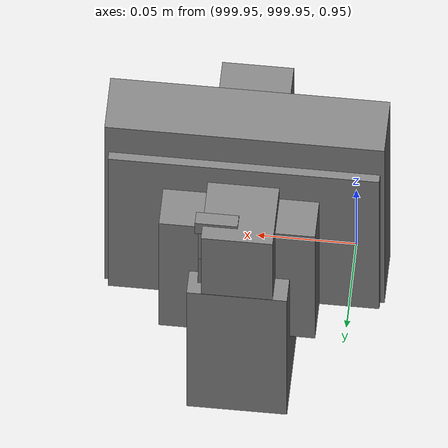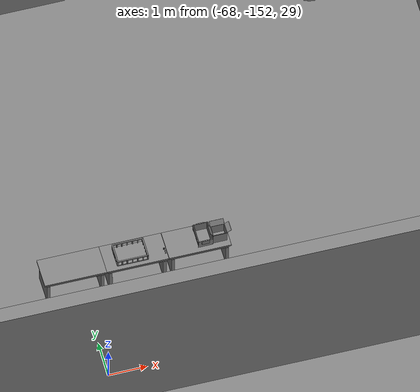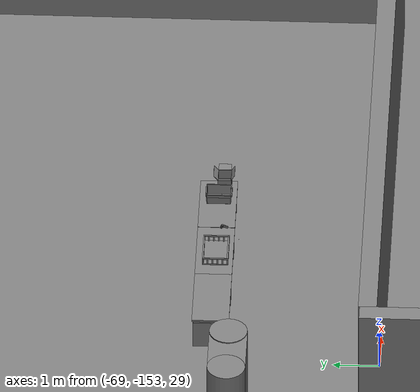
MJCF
<mujoco>
    <option gravity="0.000000000 0.000000000 -9.810000420" timestep="0.0049999999" integrator="implicitfast" density="1.225" viscosity="1.8000001e-05" noslip_iterations="10" iterations="100" sdf_iterations="50">
        <flag multiccd="disable"/>
    </option>
    <size memory="1000M"/>
    <compiler coordinate="local"/>
    <worldbody>
        <light cutoff="30" pos="0 1 1" dir="0 -1 -2"/>
        <light cutoff="30" pos="0 -1 1" dir="0 1 -2"/>
        <body pos="-64.866622925 -149.383972168 30.183746338" euler="89.999984741 89.999946594 0.000000000" name="openloong_gripper_2f85_fix_base_usda_bluebox_01">
            <geom contype="1" conaffinity="1" density="1000" type="box" material="" rgba="0.500000000 0.500000000 0.500000000 1.000000000" solimp="0.899999976 0.949999988 0.001000000" friction="1.000000000 0.005000000 0.000100000" solref="0.020000000 1.000000000" margin="0" condim="3" group="0" pos="0.276580811 0.187225342 0.000068665" quat="0.707106948 0.000077471 0.707106352 0.000077486" size="0.100000001 0.057999998 0.010000000" name="openloong_gripper_2f85_fix_base_usda_geom_F4E0E8BA_6646_4ADD_A3CF_22303BF3D404"/>
            <geom contype="1" conaffinity="1" density="1000" type="box" material="" rgba="0.500000000 0.500000000 0.500000000 1.000000000" solimp="0.899999976 0.949999988 0.001000000" friction="1.000000000 0.005000000 0.000100000" solref="0.020000000 1.000000000" margin="0" condim="3" group="0" pos="0.000000000 0.002883911 0.000000000" quat="0.999999881 0.000000000 0.000000000 0.000000000" size="0.254000008 0.003000000 0.172000006" name="openloong_gripper_2f85_fix_base_usda_geom_47A46E59_9CD4_46B7_B1C7_D9FFC37CC94B"/>
            <geom contype="1" conaffinity="1" density="1000" type="box" material="" rgba="0.500000000 0.500000000 0.500000000 1.000000000" solimp="0.899999976 0.949999988 0.001000000" friction="1.000000000 0.005000000 0.000100000" solref="0.020000000 1.000000000" margin="0" condim="3" group="0" pos="0.000000000 0.124874115 0.173484802" quat="0.999796331 0.020176515 -0.000000015 0.000000030" size="0.259999990 0.119999997 0.007000000" name="openloong_gripper_2f85_fix_base_usda_geom_5938313E_9F90_43AE_913D_FDC3122F5FB3"/>
            <geom contype="1" conaffinity="1" density="1000" type="box" material="" rgba="0.500000000 0.500000000 0.500000000 1.000000000" solimp="0.899999976 0.949999988 0.001000000" friction="1.000000000 0.005000000 0.000100000" solref="0.020000000 1.000000000" margin="0" condim="3" group="0" pos="0.000000000 0.124874115 -0.173469543" quat="0.999796331 -0.020176545 -0.000000015 0.000000000" size="0.259999990 0.119999997 0.007000000" name="openloong_gripper_2f85_fix_base_usda_geom_B8689D5E_4905_46B1_9EB6_8F6D58ECD65C"/>
            <geom contype="1" conaffinity="1" density="1000" type="box" material="" rgba="0.500000000 0.500000000 0.500000000 1.000000000" solimp="0.899999976 0.949999988 0.001000000" friction="1.000000000 0.005000000 0.000100000" solref="0.020000000 1.000000000" margin="0" condim="3" group="0" pos="0.000000000 0.214008331 0.188980103" quat="0.999912977 0.013176724 0.000000015 0.000000000" size="0.259999990 0.029999999 0.012500000" name="openloong_gripper_2f85_fix_base_usda_geom_424B2B51_5BB6_4495_945A_38128DE5AA8E"/>
            <geom contype="1" conaffinity="1" density="1000" type="box" material="" rgba="0.500000000 0.500000000 0.500000000 1.000000000" solimp="0.899999976 0.949999988 0.001000000" friction="1.000000000 0.005000000 0.000100000" solref="0.020000000 1.000000000" margin="0" condim="3" group="0" pos="-0.258361816 0.125289917 0.001876831" quat="0.702796936 -0.020792112 0.710783124 0.020769298" size="0.189999998 0.119999997 0.009000000" name="openloong_gripper_2f85_fix_base_usda_geom_466553B2_4D38_4470_B255_5DC90BDF5C72"/>
            <geom contype="1" conaffinity="1" density="1000" type="box" material="" rgba="0.500000000 0.500000000 0.500000000 1.000000000" solimp="0.899999976 0.949999988 0.001000000" friction="1.000000000 0.005000000 0.000100000" solref="0.020000000 1.000000000" margin="0" condim="3" group="0" pos="0.000000000 0.214008331 -0.188980103" quat="0.999912977 -0.013176769 0.000000030 0.000000015" size="0.259999990 0.029999999 0.012500000" name="openloong_gripper_2f85_fix_base_usda_geom_3497D70F_CCAA_47A0_BB04_E1901D2B6692"/>
            <geom contype="1" conaffinity="1" density="1000" type="box" material="" rgba="0.500000000 0.500000000 0.500000000 1.000000000" solimp="0.899999976 0.949999988 0.001000000" friction="1.000000000 0.005000000 0.000100000" solref="0.020000000 1.000000000" margin="0" condim="3" group="0" pos="-0.276611328 0.187225342 0.000068665" quat="0.707106650 0.000077441 0.707106709 0.000077456" size="0.100000001 0.057999998 0.010000000" name="openloong_gripper_2f85_fix_base_usda_geom_658A32ED_9CFC_4D19_B8E0_79E61031516F"/>
            <geom contype="1" conaffinity="1" density="1000" type="box" material="" rgba="0.500000000 0.500000000 0.500000000 1.000000000" solimp="0.899999976 0.949999988 0.001000000" friction="1.000000000 0.005000000 0.000100000" solref="0.020000000 1.000000000" margin="0" condim="3" group="0" pos="0.258331299 0.125289917 0.001876831" quat="0.702851415 0.018856421 0.710823774 -0.019329369" size="0.189999998 0.119999997 0.009000000" name="openloong_gripper_2f85_fix_base_usda_geom_952EF196_4321_487B_A264_BE441E9C79DA"/>
            <freejoint name="openloong_gripper_2f85_fix_base_usda_bluebox_01_joint"/>
            <site size="0.005000000 0.005000000 0.005000000" rgba="0.500000000 0.500000000 0.500000000 1.000000000" pos="0.000000000 0.000000000 0.000000000" quat="0.999961913 0.008726534 0.000000000 0.000000000" group="0" type="sphere" name="openloong_gripper_2f85_fix_base_usda_bluebox_01site"/>
        </body>
        <body pos="-64.496299744 -149.491867065 30.235729218" euler="0.000000000 0.000000000 89.999946594" name="openloong_gripper_2f85_fix_base_usda_cardboardbox_01">
            <geom contype="1" conaffinity="1" density="1000" type="box" material="" rgba="0.500000000 0.500000000 0.500000000 1.000000000" solimp="0.899999976 0.949999988 0.001000000" friction="1.000000000 0.005000000 0.000100000" solref="0.020000000 1.000000000" margin="0" condim="3" group="0" pos="-0.003166199 -0.004086494 0.005052090" quat="1.000000000 0.000000000 0.000000000 0.000000000" size="0.142499998 0.177500010 0.005000000" name="openloong_gripper_2f85_fix_base_usda_geom_316BAD39_4A8D_415A_8F1C_6855D49F30E7"/>
            <geom contype="1" conaffinity="1" density="1000" type="box" material="" rgba="0.500000000 0.500000000 0.500000000 1.000000000" solimp="0.899999976 0.949999988 0.001000000" friction="1.000000000 0.005000000 0.000100000" solref="0.020000000 1.000000000" margin="0" condim="3" group="0" pos="-0.003166199 0.170316696 0.150570869" quat="1.000000000 0.000000000 0.000000000 0.000000000" size="0.142499998 0.005000000 0.149999991" name="openloong_gripper_2f85_fix_base_usda_geom_BC5486BA_39B0_494E_B1CB_AB05D90F2E22"/>
            <geom contype="1" conaffinity="1" density="1000" type="box" material="" rgba="0.500000000 0.500000000 0.500000000 1.000000000" solimp="0.899999976 0.949999988 0.001000000" friction="1.000000000 0.005000000 0.000100000" solref="0.020000000 1.000000000" margin="0" condim="3" group="0" pos="-0.147399902 -0.005307198 0.150570869" quat="1.000000000 0.000000000 0.000000000 0.000000000" size="0.005000000 0.177500010 0.149999991" name="openloong_gripper_2f85_fix_base_usda_geom_5934331D_FBF3_41E9_8355_6B5B3B261281"/>
            <geom contype="1" conaffinity="1" density="1000" type="box" material="" rgba="0.500000000 0.500000000 0.500000000 1.000000000" solimp="0.899999976 0.949999988 0.001000000" friction="1.000000000 0.005000000 0.000100000" solref="0.020000000 1.000000000" margin="0" condim="3" group="0" pos="0.140275955 -0.005307198 0.150570869" quat="1.000000000 0.000000000 0.000000000 0.000000000" size="0.005000000 0.177500010 0.149999991" name="openloong_gripper_2f85_fix_base_usda_geom_19C11959_9355_4075_8B99_67F840DF0AB4"/>
            <geom contype="1" conaffinity="1" density="1000" type="box" material="" rgba="0.500000000 0.500000000 0.500000000 1.000000000" solimp="0.899999976 0.949999988 0.001000000" friction="1.000000000 0.005000000 0.000100000" solref="0.020000000 1.000000000" margin="0" condim="3" group="0" pos="-0.003166199 -0.181550980 0.150570869" quat="1.000000000 0.000000000 0.000000000 0.000000000" size="0.142499998 0.005000000 0.149999991" name="openloong_gripper_2f85_fix_base_usda_geom_01B24F08_F80B_496B_A1D6_A10BFCD9BD50"/>
            <freejoint name="openloong_gripper_2f85_fix_base_usda_cardboardbox_01_joint"/>
            <site size="0.005000000 0.005000000 0.005000000" rgba="0.500000000 0.500000000 0.500000000 1.000000000" pos="0.000000000 0.000000000 0.000000000" quat="0.999961913 0.008726535 0.000000000 0.000000000" group="0" type="sphere" name="openloong_gripper_2f85_fix_base_usda_site_C07D90A4_41BA_49B6_BC8B_AE8B0B3D3AF2"/>
            <body pos="0.139160156 -0.004048347 0.301930904" euler="-179.999954224 49.383502960 179.999954224" name="openloong_gripper_2f85_fix_base_usda_A1_006">
                <geom contype="1" conaffinity="1" density="1000" type="box" material="" rgba="0.500000000 0.500000000 0.500000000 1.000000000" solimp="0.899999976 0.949999988 0.001000000" friction="1.000000000 0.005000000 0.000100000" solref="0.020000000 1.000000000" margin="0" condim="3" group="0" pos="-0.071587563 0.000009537 0.001745224" quat="0.999999881 0.000000000 0.000000000 0.000000000" size="0.071249999 0.179999992 0.002500000" name="openloong_gripper_2f85_fix_base_usda_geom_756A66B4_CA7C_4A5B_94C8_CB4AAD12804E"/>
                <joint armature="0" stiffness="0.07" damping="0.0099999998" axis="0.000000 1.000000 0.000000" type="hinge" name="openloong_gripper_2f85_fix_base_usda_A1_006"/>
            </body>
            <body pos="-0.145902634 -0.004086494 0.301938057" euler="-180.000000000 -60.000011444 -180.000000000" name="openloong_gripper_2f85_fix_base_usda_A2_006">
                <geom contype="1" conaffinity="1" density="1000" type="box" material="" rgba="0.500000000 0.500000000 0.500000000 1.000000000" solimp="0.899999976 0.949999988 0.001000000" friction="1.000000000 0.005000000 0.000100000" solref="0.020000000 1.000000000" margin="0" condim="3" group="0" pos="0.071268082 0.000009537 0.002717972" quat="0.000002921 0.000000000 -0.000000030 0.999999881" size="0.071249999 0.179999992 0.002500000" name="openloong_gripper_2f85_fix_base_usda_geom_3439D1EF_1249_49FF_9326_A8B740E91432"/>
                <joint armature="0" stiffness="0.07" damping="0.0099999998" axis="0.000000 1.000000 0.000000" type="hinge" name="openloong_gripper_2f85_fix_base_usda_A2_006"/>
            </body>
            <body pos="-0.003385544 0.175991058 0.301930904" euler="-125.858116150 -0.000004561 0.000002331" name="openloong_gripper_2f85_fix_base_usda_B2_006">
                <geom contype="1" conaffinity="1" density="1000" type="box" material="" rgba="0.500000000 0.500000000 0.500000000 1.000000000" solimp="0.899999976 0.949999988 0.001000000" friction="1.000000000 0.005000000 0.000100000" solref="0.020000000 1.000000000" margin="0" condim="3" group="0" pos="0.000009537 -0.070939064 -0.002470016" quat="0.999614120 0.027776197 -0.000000015 0.000000030" size="0.137500003 0.064999998 0.005000000" name="openloong_gripper_2f85_fix_base_usda_geom_FA35C0DD_D7ED_4550_853D_D6F4DB294396"/>
                <joint armature="0" stiffness="0.07" damping="0.0099999998" axis="1.000000 0.000000 0.000000" type="hinge" name="openloong_gripper_2f85_fix_base_usda_B2_006"/>
            </body>
            <body pos="-0.003385544 -0.184140205 0.301938057" euler="147.805557251 0.000000000 0.000000000" name="openloong_gripper_2f85_fix_base_usda_B1_006">
                <geom contype="1" conaffinity="1" density="1000" type="box" material="" rgba="0.500000000 0.500000000 0.500000000 1.000000000" solimp="0.899999976 0.949999988 0.001000000" friction="1.000000000 0.005000000 0.000100000" solref="0.020000000 1.000000000" margin="0" condim="3" group="0" pos="-0.000028610 0.070202351 -0.002703667" quat="0.999614179 -0.027776167 0.000000000 0.000000000" size="0.137500003 0.064999998 0.005000000" name="openloong_gripper_2f85_fix_base_usda_geom_8F56A0BF_F820_4E4E_BA3B_F9D2AD082CC5"/>
                <joint armature="0" stiffness="0.07" damping="0.0099999998" axis="1.000000 0.000000 0.000000" type="hinge" name="openloong_gripper_2f85_fix_base_usda_B1_006"/>
            </body>
        </body>
        <body pos="-65.882858276 -149.481979370 30.229999542" euler="-64.487716675 0.000000000 0.000000000" name="openloong_gripper_2f85_fix_base_usda_Barcode">
            <geom contype="1" conaffinity="1" density="1000" type="box" material="" rgba="0.500000000 0.500000000 0.500000000 1.000000000" solimp="0.899999976 0.949999988 0.001000000" friction="1.000000000 0.005000000 0.000100000" solref="0.020000000 1.000000000" margin="0" condim="3" group="0" pos="0.000000000 0.013038635 0.001419067" quat="0.000000000 0.000000000 0.000000000 1.000000119" size="0.034000002 0.010000000 0.017999999" name="openloong_gripper_2f85_fix_base_usda_geom_10DE2EDF_987D_4E6A_89E6_D7677F5FC030"/>
            <geom contype="1" conaffinity="1" density="1000" type="box" material="" rgba="0.500000000 0.500000000 0.500000000 1.000000000" solimp="0.899999976 0.949999988 0.001000000" friction="1.000000000 0.005000000 0.000100000" solref="0.020000000 1.000000000" margin="0" condim="3" group="0" pos="0.000000000 -0.035301208 -0.007095337" quat="0.000000000 0.000000000 -0.043619365 0.999048233" size="0.028999999 0.010000000 0.020000000" name="openloong_gripper_2f85_fix_base_usda_geom_28E8E3C2_CB7E_48B3_BDB6_1BB8D588157C"/>
            <geom contype="1" conaffinity="1" density="1000" type="box" material="" rgba="0.500000000 0.500000000 0.500000000 1.000000000" solimp="0.899999976 0.949999988 0.001000000" friction="1.000000000 0.005000000 0.000100000" solref="0.020000000 1.000000000" margin="0" condim="3" group="0" pos="0.000000000 -0.043411255 -0.011749268" quat="0.922262907 0.386563420 0.000000000 0.000000000" size="0.026000001 0.010000000 0.020000000" name="openloong_gripper_2f85_fix_base_usda_geom_79DE314C_E86B_4516_919E_266BFF35F0E6"/>
            <geom contype="1" conaffinity="1" density="1000" type="box" material="" rgba="0.500000000 0.500000000 0.500000000 1.000000000" solimp="0.899999976 0.949999988 0.001000000" friction="1.000000000 0.005000000 0.000100000" solref="0.020000000 1.000000000" margin="0" condim="3" group="0" pos="0.000000000 -0.016967773 -0.031860352" quat="0.000000000 0.000000000 0.000000000 1.000000119" size="0.008000000 0.010000000 0.013000000" name="openloong_gripper_2f85_fix_base_usda_geom_6CFDE71C_A3F7_4410_92EF_DFD1B4A9EEF5"/>
            <geom contype="1" conaffinity="1" density="1000" type="box" material="" rgba="0.500000000 0.500000000 0.500000000 1.000000000" solimp="0.899999976 0.949999988 0.001000000" friction="1.000000000 0.005000000 0.000100000" solref="0.020000000 1.000000000" margin="0" condim="3" group="0" pos="0.000000000 -0.001869202 0.000312805" quat="0.953716993 0.300705761 0.000000000 0.000000000" size="0.032000002 0.010000000 0.018999999" name="openloong_gripper_2f85_fix_base_usda_geom_2DA9A7CF_E791_48D8_9E32_6ED9F510C80D"/>
            <geom contype="1" conaffinity="1" density="1000" type="box" material="" rgba="0.500000000 0.500000000 0.500000000 1.000000000" solimp="0.899999976 0.949999988 0.001000000" friction="1.000000000 0.005000000 0.000100000" solref="0.020000000 1.000000000" margin="0" condim="3" group="0" pos="0.000000000 -0.019531250 -0.003173828" quat="0.953716993 0.300705761 0.000000000 0.000000000" size="0.030999999 0.010000000 0.020000000" name="openloong_gripper_2f85_fix_base_usda_geom_994891B8_ADF6_48C9_B4D5_67BC28CB769D"/>
            <geom contype="1" conaffinity="1" density="1000" type="box" material="" rgba="0.500000000 0.500000000 0.500000000 1.000000000" solimp="0.899999976 0.949999988 0.001000000" friction="1.000000000 0.005000000 0.000100000" solref="0.020000000 1.000000000" margin="0" condim="3" group="0" pos="0.000000000 -0.035301208 -0.007095337" quat="0.953716993 0.300705761 0.000000000 0.000000000" size="0.028999999 0.010000000 0.020000000" name="openloong_gripper_2f85_fix_base_usda_geom_46217516_A483_4D0D_B706_3228E05D9368"/>
            <geom contype="1" conaffinity="1" density="1000" type="box" material="" rgba="0.500000000 0.500000000 0.500000000 1.000000000" solimp="0.899999976 0.949999988 0.001000000" friction="1.000000000 0.005000000 0.000100000" solref="0.020000000 1.000000000" margin="0" condim="3" group="0" pos="0.000000000 -0.042617798 -0.071121216" quat="0.000000000 0.000000000 0.000000000 1.000000119" size="0.013000000 0.021000000 0.059999999" name="openloong_gripper_2f85_fix_base_usda_geom_C3027025_45E3_48EA_B972_395B81129230"/>
            <freejoint name="openloong_gripper_2f85_fix_base_usda_Barcode_joint"/>
            <site size="0.005000000 0.005000000 0.005000000" rgba="0.500000000 0.500000000 0.500000000 1.000000000" pos="0.000000000 0.000000000 0.000000000" quat="1.000000000 0.000000000 0.000000000 0.000000000" group="0" type="sphere" name="openloong_gripper_2f85_fix_base_usda_Barcode_site"/>
        </body>
        <body pos="-66.745018005 -149.392349243 30.184000015" euler="0.000000000 0.000000000 89.999946594" name="[22331343190020]_Basket_01">
            <geom contype="1" conaffinity="1" density="1000" type="box" material="" rgba="0.500000000 0.500000000 0.500000000 1.000000000" solimp="0.899999976 0.949999988 0.001000000" friction="1.000000000 0.005000000 0.000100000" solref="0.020000000 1.000000000" margin="0" condim="3" group="0" pos="-0.052425385 0.389207840 0.089787483" quat="0.707107008 0.000000000 0.000000000 0.707106411" size="0.014249999 0.014249999 0.059999999" name="[22331343190020]_geom_FC77CBA7_A451_4AD5_BB39_DFC46361B2D4"/>
            <geom contype="1" conaffinity="1" density="1000" type="box" material="" rgba="0.500000000 0.500000000 0.500000000 1.000000000" solimp="0.899999976 0.949999988 0.001000000" friction="1.000000000 0.005000000 0.000100000" solref="0.020000000 1.000000000" margin="0" condim="3" group="0" pos="0.264015198 -0.133043289 0.089787483" quat="0.707107008 0.000000000 0.000000000 0.707106411" size="0.014249999 0.014249999 0.059999999" name="[22331343190020]_geom_F1A5C753_5995_4C69_92AB_D844781EE50F"/>
            <geom contype="1" conaffinity="1" density="1000" type="box" material="" rgba="0.500000000 0.500000000 0.500000000 1.000000000" solimp="0.899999976 0.949999988 0.001000000" friction="1.000000000 0.005000000 0.000100000" solref="0.020000000 1.000000000" margin="0" condim="3" group="0" pos="-0.264015198 -0.265548706 0.089793205" quat="0.707107008 0.000000000 0.000000000 0.707106411" size="0.014249999 0.014249999 0.059999999" name="[22331343190020]_geom_D3E5E0D0_8997_45C8_8B0D_1114C60C66A7"/>
            <geom contype="1" conaffinity="1" density="1000" type="box" material="" rgba="0.500000000 0.500000000 0.500000000 1.000000000" solimp="0.899999976 0.949999988 0.001000000" friction="1.000000000 0.005000000 0.000100000" solref="0.020000000 1.000000000" margin="0" condim="3" group="0" pos="-0.160263062 -0.389322281 0.089793205" quat="0.707107008 0.000000000 0.000000000 0.707106411" size="0.014249999 0.014249999 0.059999999" name="[22331343190020]_geom_FAF2037E_6C00_4561_8A9F_7F7D14B0FD31"/>
            <geom contype="1" conaffinity="1" density="1000" type="box" material="" rgba="0.500000000 0.500000000 0.500000000 1.000000000" solimp="0.899999976 0.949999988 0.001000000" friction="1.000000000 0.005000000 0.000100000" solref="0.020000000 1.000000000" margin="0" condim="3" group="0" pos="0.162265778 -0.389322281 0.089787483" quat="0.707107008 0.000000000 0.000000000 0.707106411" size="0.014249999 0.014249999 0.059999999" name="[22331343190020]_geom_D50773BA_6DDA_430F_8151_9B60C4A145BD"/>
            <geom contype="1" conaffinity="1" density="1000" type="box" material="" rgba="0.500000000 0.500000000 0.500000000 1.000000000" solimp="0.899999976 0.949999988 0.001000000" friction="1.000000000 0.005000000 0.000100000" solref="0.020000000 1.000000000" margin="0" condim="3" group="0" pos="0.264015198 0.389207840 0.089787483" quat="0.707107008 0.000000000 0.000000000 0.707106411" size="0.014249999 0.014249999 0.059999999" name="[22331343190020]_geom_E3DE6F2B_4318_4B4E_AEBB_3C105AF508D3"/>
            <geom contype="1" conaffinity="1" density="1000" type="box" material="" rgba="0.500000000 0.500000000 0.500000000 1.000000000" solimp="0.899999976 0.949999988 0.001000000" friction="1.000000000 0.005000000 0.000100000" solref="0.020000000 1.000000000" margin="0" condim="3" group="0" pos="-0.264015198 -0.133043289 0.089793205" quat="0.707107008 0.000000000 0.000000000 0.707106411" size="0.014249999 0.014249999 0.059999999" name="[22331343190020]_geom_D2F6CF28_B676_473B_A66E_2957C78828DB"/>
            <geom contype="1" conaffinity="1" density="1000" type="box" material="" rgba="0.500000000 0.500000000 0.500000000 1.000000000" solimp="0.899999976 0.949999988 0.001000000" friction="1.000000000 0.005000000 0.000100000" solref="0.020000000 1.000000000" margin="0" condim="3" group="0" pos="-0.264026642 0.269256592 0.089793205" quat="0.707107008 0.000000000 0.000000000 0.707106411" size="0.014249999 0.014249999 0.059999999" name="[22331343190020]_geom_99A6A158_8AA5_457A_B383_95687802A402"/>
            <geom contype="1" conaffinity="1" density="1000" type="box" material="" rgba="0.500000000 0.500000000 0.500000000 1.000000000" solimp="0.899999976 0.949999988 0.001000000" friction="1.000000000 0.005000000 0.000100000" solref="0.020000000 1.000000000" margin="0" condim="3" group="0" pos="0.054462433 0.389207840 0.089787483" quat="0.707107008 0.000000000 0.000000000 0.707106411" size="0.014249999 0.014249999 0.059999999" name="[22331343190020]_geom_8B27374F_3938_400F_9528_F49CC4DB4844"/>
            <geom contype="1" conaffinity="1" density="1000" type="box" material="" rgba="0.500000000 0.500000000 0.500000000 1.000000000" solimp="0.899999976 0.949999988 0.001000000" friction="1.000000000 0.005000000 0.000100000" solref="0.020000000 1.000000000" margin="0" condim="3" group="0" pos="0.054462433 -0.389322281 0.089787483" quat="0.707107008 0.000000000 0.000000000 0.707106411" size="0.014249999 0.014249999 0.059999999" name="[22331343190020]_geom_475969A3_8FBD_4017_9116_9C05C9077524"/>
            <geom contype="1" conaffinity="1" density="1000" type="box" material="" rgba="0.500000000 0.500000000 0.500000000 1.000000000" solimp="0.899999976 0.949999988 0.001000000" friction="1.000000000 0.005000000 0.000100000" solref="0.020000000 1.000000000" margin="0" condim="3" group="0" pos="0.264015198 0.269256592 0.089793205" quat="0.707107008 0.000000000 0.000000000 0.707106411" size="0.014249999 0.014249999 0.059999999" name="[22331343190020]_geom_514EB7F8_6EC2_41E6_A617_0EDB256A10A6"/>
            <geom contype="1" conaffinity="1" density="1000" type="box" material="" rgba="0.500000000 0.500000000 0.500000000 1.000000000" solimp="0.899999976 0.949999988 0.001000000" friction="1.000000000 0.005000000 0.000100000" solref="0.020000000 1.000000000" margin="0" condim="3" group="0" pos="0.264015198 -0.389322281 0.089787483" quat="0.707107008 0.000000000 0.000000000 0.707106411" size="0.014249999 0.014249999 0.059999999" name="[22331343190020]_geom_AE929659_3AF3_4CB2_B725_B3C92EE3D141"/>
            <geom contype="1" conaffinity="1" density="1000" type="box" material="" rgba="0.500000000 0.500000000 0.500000000 1.000000000" solimp="0.899999976 0.949999988 0.001000000" friction="1.000000000 0.005000000 0.000100000" solref="0.020000000 1.000000000" margin="0" condim="3" group="0" pos="0.000000000 0.000000000 0.015998840" quat="0.707107008 0.000000000 0.000000000 0.707106411" size="0.403499991 0.279000014 0.015750000" name="[22331343190020]_geom_5A624100_FBFE_4837_8B56_2356B8F22C47"/>
            <geom contype="1" conaffinity="1" density="1000" type="box" material="" rgba="0.500000000 0.500000000 0.500000000 1.000000000" solimp="0.899999976 0.949999988 0.001000000" friction="1.000000000 0.005000000 0.000100000" solref="0.020000000 1.000000000" margin="0" condim="3" group="0" pos="0.000000000 -0.389476776 0.163619041" quat="0.707107008 0.000000000 0.000000000 0.707106411" size="0.015000000 0.277500004 0.015750000" name="[22331343190020]_geom_DFC764B7_3DC9_4AF3_9A99_55DB6028E965"/>
            <geom contype="1" conaffinity="1" density="1000" type="box" material="" rgba="0.500000000 0.500000000 0.500000000 1.000000000" solimp="0.899999976 0.949999988 0.001000000" friction="1.000000000 0.005000000 0.000100000" solref="0.020000000 1.000000000" margin="0" condim="3" group="0" pos="0.162265778 0.389207840 0.089787483" quat="0.707107008 0.000000000 0.000000000 0.707106411" size="0.014249999 0.014249999 0.059999999" name="[22331343190020]_geom_DE8B76BA_B405_4250_B522_05E5099EB52A"/>
            <geom contype="1" conaffinity="1" density="1000" type="box" material="" rgba="0.500000000 0.500000000 0.500000000 1.000000000" solimp="0.899999976 0.949999988 0.001000000" friction="1.000000000 0.005000000 0.000100000" solref="0.020000000 1.000000000" margin="0" condim="3" group="0" pos="0.000000000 0.389471054 0.163619041" quat="0.707107008 0.000000000 0.000000000 0.707106411" size="0.015000000 0.277500004 0.015750000" name="[22331343190020]_geom_A9AA852E_1AC4_4D9A_93EA_DB29754B5708"/>
            <geom contype="1" conaffinity="1" density="1000" type="box" material="" rgba="0.500000000 0.500000000 0.500000000 1.000000000" solimp="0.899999976 0.949999988 0.001000000" friction="1.000000000 0.005000000 0.000100000" solref="0.020000000 1.000000000" margin="0" condim="3" group="0" pos="-0.263511658 0.000000000 0.163619041" quat="0.707107008 0.000000000 0.000000000 0.707106411" size="0.403499991 0.015000000 0.015750000" name="[22331343190020]_geom_8595638B_F628_4C0B_81B7_FD01CBF415C6"/>
            <geom contype="1" conaffinity="1" density="1000" type="box" material="" rgba="0.500000000 0.500000000 0.500000000 1.000000000" solimp="0.899999976 0.949999988 0.001000000" friction="1.000000000 0.005000000 0.000100000" solref="0.020000000 1.000000000" margin="0" condim="3" group="0" pos="-0.264015198 0.141334534 0.089793205" quat="0.707107008 0.000000000 0.000000000 0.707106411" size="0.014249999 0.014249999 0.059999999" name="[22331343190020]_geom_6669AC67_8652_403A_BCC2_27F41EBC15E4"/>
            <geom contype="1" conaffinity="1" density="1000" type="box" material="" rgba="0.500000000 0.500000000 0.500000000 1.000000000" solimp="0.899999976 0.949999988 0.001000000" friction="1.000000000 0.005000000 0.000100000" solref="0.020000000 1.000000000" margin="0" condim="3" group="0" pos="0.264015198 -0.265548706 0.089787483" quat="0.707107008 0.000000000 0.000000000 0.707106411" size="0.014249999 0.014249999 0.059999999" name="[22331343190020]_geom_6C50BD03_AE1E_48A4_8F02_ED0C62859428"/>
            <geom contype="1" conaffinity="1" density="1000" type="box" material="" rgba="0.500000000 0.500000000 0.500000000 1.000000000" solimp="0.899999976 0.949999988 0.001000000" friction="1.000000000 0.005000000 0.000100000" solref="0.020000000 1.000000000" margin="0" condim="3" group="0" pos="-0.160263062 0.389207840 0.089787483" quat="0.707107008 0.000000000 0.000000000 0.707106411" size="0.014249999 0.014249999 0.059999999" name="[22331343190020]_geom_662B662F_C1E8_44BE_AEA4_E29EDDC2BCD4"/>
            <geom contype="1" conaffinity="1" density="1000" type="box" material="" rgba="0.500000000 0.500000000 0.500000000 1.000000000" solimp="0.899999976 0.949999988 0.001000000" friction="1.000000000 0.005000000 0.000100000" solref="0.020000000 1.000000000" margin="0" condim="3" group="0" pos="-0.052425385 -0.389322281 0.089787483" quat="0.707107008 0.000000000 0.000000000 0.707106411" size="0.014249999 0.014249999 0.059999999" name="[22331343190020]_geom_8B264D53_09CB_4E72_95D7_578FE6BCEE99"/>
            <geom contype="1" conaffinity="1" density="1000" type="box" material="" rgba="0.500000000 0.500000000 0.500000000 1.000000000" solimp="0.899999976 0.949999988 0.001000000" friction="1.000000000 0.005000000 0.000100000" solref="0.020000000 1.000000000" margin="0" condim="3" group="0" pos="-0.264026642 -0.389322281 0.089793205" quat="0.707107008 0.000000000 0.000000000 0.707106411" size="0.014249999 0.014249999 0.059999999" name="[22331343190020]_geom_E3FDFA8A_1175_4337_96E3_B7E7BF4A3471"/>
            <geom contype="1" conaffinity="1" density="1000" type="box" material="" rgba="0.500000000 0.500000000 0.500000000 1.000000000" solimp="0.899999976 0.949999988 0.001000000" friction="1.000000000 0.005000000 0.000100000" solref="0.020000000 1.000000000" margin="0" condim="3" group="0" pos="0.264015198 0.141334534 0.089787483" quat="0.707107008 0.000000000 0.000000000 0.707106411" size="0.014249999 0.014249999 0.059999999" name="[22331343190020]_geom_6CB611F7_4349_4747_BE7D_07BCEEE71C32"/>
            <geom contype="1" conaffinity="1" density="1000" type="box" material="" rgba="0.500000000 0.500000000 0.500000000 1.000000000" solimp="0.899999976 0.949999988 0.001000000" friction="1.000000000 0.005000000 0.000100000" solref="0.020000000 1.000000000" margin="0" condim="3" group="0" pos="-0.264015198 0.389207840 0.089793205" quat="0.707107008 0.000000000 0.000000000 0.707106411" size="0.014249999 0.014249999 0.059999999" name="[22331343190020]_geom_5552A485_DC02_4ABE_B087_919CA653FF64"/>
            <geom contype="1" conaffinity="1" density="1000" type="box" material="" rgba="0.500000000 0.500000000 0.500000000 1.000000000" solimp="0.899999976 0.949999988 0.001000000" friction="1.000000000 0.005000000 0.000100000" solref="0.020000000 1.000000000" margin="0" condim="3" group="0" pos="0.264015198 0.004480362 0.089787483" quat="0.707107008 0.000000000 0.000000000 0.707106411" size="0.014249999 0.014249999 0.059999999" name="[22331343190020]_geom_576DF7FF_825C_4FCF_97AD_AC8E537E30A4"/>
            <geom contype="1" conaffinity="1" density="1000" type="box" material="" rgba="0.500000000 0.500000000 0.500000000 1.000000000" solimp="0.899999976 0.949999988 0.001000000" friction="1.000000000 0.005000000 0.000100000" solref="0.020000000 1.000000000" margin="0" condim="3" group="0" pos="0.263694763 -0.000011444 0.163619041" quat="0.707107008 0.000000000 0.000000000 0.707106411" size="0.403499991 0.015000000 0.015750000" name="[22331343190020]_geom_4E7CA93C_93E8_4718_829C_5247B0226380"/>
            <geom contype="1" conaffinity="1" density="1000" type="box" material="" rgba="0.500000000 0.500000000 0.500000000 1.000000000" solimp="0.899999976 0.949999988 0.001000000" friction="1.000000000 0.005000000 0.000100000" solref="0.020000000 1.000000000" margin="0" condim="3" group="0" pos="-0.264015198 0.004480362 0.089793205" quat="0.707107008 0.000000000 0.000000000 0.707106411" size="0.014249999 0.014249999 0.059999999" name="[22331343190020]_geom_A5BD392F_9651_4BF0_928C_99B2225C88DA"/>
            <freejoint name="[22331343190020]_joint_03209188_106E_42C9_85B6_149E315344F5"/>
        </body>
        <body pos="0.000000000 0.000000000 0.000000000" euler="0.000000000 0.000000000 0.000000000" name="Static Objects_Static Objects">
            <geom contype="1" conaffinity="1" density="1000" type="box" material="" rgba="0.500000000 0.500000000 0.500000000 1.000000000" solimp="0.899999976 0.949999988 0.001000000" friction="1.000000000 0.005000000 0.000100000" solref="0.020000000 1.000000000" margin="0" condim="3" group="0" pos="-67.544113159 -149.365814209 29.727830887" quat="0.500000417 0.499999970 0.499999553 0.499999970" size="0.381000012 0.319999993 0.041000001" name="Static Objects_geom_13063F7C_A80C_45F4_9302_E3E9ABFC237C"/>
            <geom contype="1" conaffinity="1" density="1000" type="box" material="" rgba="0.500000000 0.500000000 0.500000000 1.000000000" solimp="0.899999976 0.949999988 0.001000000" friction="1.000000000 0.005000000 0.000100000" solref="0.020000000 1.000000000" margin="0" condim="3" group="0" pos="-68.239501953 -149.365814209 30.086868286" quat="0.500000417 0.499999970 0.499999553 0.499999970" size="0.370999992 0.039500002 0.745000005" name="Static Objects_geom_64A56266_5C1C_4BFF_91BE_14A7D1343128"/>
            <geom contype="1" conaffinity="1" density="1000" type="box" material="" rgba="0.500000000 0.500000000 0.500000000 1.000000000" solimp="0.899999976 0.949999988 0.001000000" friction="1.000000000 0.005000000 0.000100000" solref="0.020000000 1.000000000" margin="0" condim="3" group="0" pos="-68.239501953 -149.365814209 30.147235870" quat="0.500000417 0.499999970 0.499999553 0.499999970" size="0.400000006 0.022000000 0.800000012" name="Static Objects_geom_46A49100_265B_496F_AA0A_651BC4F64D20"/>
            <geom contype="1" conaffinity="1" density="1000" type="box" material="" rgba="0.500000000 0.500000000 0.500000000 1.000000000" solimp="0.899999976 0.949999988 0.001000000" friction="1.000000000 0.005000000 0.000100000" solref="0.020000000 1.000000000" margin="0" condim="3" group="0" pos="-68.934890747 -149.365814209 29.727830887" quat="0.500000417 0.499999970 0.499999553 0.499999970" size="0.381000012 0.319999993 0.041000001" name="Static Objects_geom_92FE0B7B_AFA3_4186_AAC2_C73A8F520EEC"/>
            <geom contype="1" conaffinity="1" density="1000" type="box" material="" rgba="0.500000000 0.500000000 0.500000000 1.000000000" solimp="0.899999976 0.949999988 0.001000000" friction="1.000000000 0.005000000 0.000100000" solref="0.020000000 1.000000000" margin="0" condim="3" group="0" pos="-68.239501953 -149.365814209 29.561563492" quat="0.500000417 0.499999970 0.499999553 0.499999970" size="0.020000000 0.022000000 0.660000026" name="Static Objects_geom_92C727D1_06B1_4EF7_8C42_EE8C395AD1EB"/>
            <geom contype="1" conaffinity="1" density="1000" type="box" material="" rgba="0.500000000 0.500000000 0.500000000 1.000000000" solimp="0.899999976 0.949999988 0.001000000" friction="1.000000000 0.005000000 0.000100000" solref="0.020000000 1.000000000" margin="0" condim="3" group="0" pos="-65.945671082 -149.365814209 29.727830887" quat="0.500000417 0.499999970 0.499999553 0.499999970" size="0.381000012 0.319999993 0.041000001" name="Static Objects_geom_5847E84B_A7DA_4110_A782_B8652F0A9C44"/>
            <geom contype="1" conaffinity="1" density="1000" type="box" material="" rgba="0.500000000 0.500000000 0.500000000 1.000000000" solimp="0.899999976 0.949999988 0.001000000" friction="1.000000000 0.005000000 0.000100000" solref="0.020000000 1.000000000" margin="0" condim="3" group="0" pos="-66.641059875 -149.365814209 30.086868286" quat="0.500000417 0.499999970 0.499999553 0.499999970" size="0.370999992 0.039500002 0.745000005" name="Static Objects_geom_794EC739_D3DF_4A1C_BA13_B90B3E31FA85"/>
            <geom contype="1" conaffinity="1" density="1000" type="box" material="" rgba="0.500000000 0.500000000 0.500000000 1.000000000" solimp="0.899999976 0.949999988 0.001000000" friction="1.000000000 0.005000000 0.000100000" solref="0.020000000 1.000000000" margin="0" condim="3" group="0" pos="-66.641059875 -149.365814209 30.147235870" quat="0.500000417 0.499999970 0.499999553 0.499999970" size="0.400000006 0.022000000 0.800000012" name="Static Objects_geom_98586A64_2A89_4D63_8565_D1ECB5A303AD"/>
            <geom contype="1" conaffinity="1" density="1000" type="box" material="" rgba="0.500000000 0.500000000 0.500000000 1.000000000" solimp="0.899999976 0.949999988 0.001000000" friction="1.000000000 0.005000000 0.000100000" solref="0.020000000 1.000000000" margin="0" condim="3" group="0" pos="-67.336448669 -149.365814209 29.727830887" quat="0.500000417 0.499999970 0.499999553 0.499999970" size="0.381000012 0.319999993 0.041000001" name="Static Objects_geom_A4E87F59_6FD6_4D38_9B06_F5DC0BB44E06"/>
            <geom contype="1" conaffinity="1" density="1000" type="box" material="" rgba="0.500000000 0.500000000 0.500000000 1.000000000" solimp="0.899999976 0.949999988 0.001000000" friction="1.000000000 0.005000000 0.000100000" solref="0.020000000 1.000000000" margin="0" condim="3" group="0" pos="-66.641059875 -149.365814209 29.561563492" quat="0.500000417 0.499999970 0.499999553 0.499999970" size="0.020000000 0.022000000 0.660000026" name="Static Objects_geom_642D4127_83AD_4809_8E03_17727ABA8FE2"/>
            <geom contype="1" conaffinity="1" density="1000" type="box" material="" rgba="0.500000000 0.500000000 0.500000000 1.000000000" solimp="0.899999976 0.949999988 0.001000000" friction="1.000000000 0.005000000 0.000100000" solref="0.020000000 1.000000000" margin="0" condim="3" group="0" pos="-64.338577271 -149.365814209 29.727830887" quat="0.500000417 0.499999970 0.499999553 0.499999970" size="0.381000012 0.319999993 0.041000001" name="Static Objects_geom_882764B3_5E46_4D9B_B7BB_FA2392B77328"/>
            <geom contype="1" conaffinity="1" density="1000" type="box" material="" rgba="0.500000000 0.500000000 0.500000000 1.000000000" solimp="0.899999976 0.949999988 0.001000000" friction="1.000000000 0.005000000 0.000100000" solref="0.020000000 1.000000000" margin="0" condim="3" group="0" pos="-65.033966064 -149.365814209 30.086868286" quat="0.500000417 0.499999970 0.499999553 0.499999970" size="0.370999992 0.039500002 0.745000005" name="Static Objects_geom_B6959079_B351_4C8A_A616_A951683928DD"/>
            <geom contype="1" conaffinity="1" density="1000" type="box" material="" rgba="0.500000000 0.500000000 0.500000000 1.000000000" solimp="0.899999976 0.949999988 0.001000000" friction="1.000000000 0.005000000 0.000100000" solref="0.020000000 1.000000000" margin="0" condim="3" group="0" pos="-65.033966064 -149.365814209 30.147235870" quat="0.500000417 0.499999970 0.499999553 0.499999970" size="0.400000006 0.022000000 0.800000012" name="Static Objects_geom_15759F57_0F71_44FD_9585_618E03F442A1"/>
            <geom contype="1" conaffinity="1" density="1000" type="box" material="" rgba="0.500000000 0.500000000 0.500000000 1.000000000" solimp="0.899999976 0.949999988 0.001000000" friction="1.000000000 0.005000000 0.000100000" solref="0.020000000 1.000000000" margin="0" condim="3" group="0" pos="-65.729354858 -149.365814209 29.727830887" quat="0.500000417 0.499999970 0.499999553 0.499999970" size="0.381000012 0.319999993 0.041000001" name="Static Objects_geom_B18A4105_64D4_4CCE_91E9_8D73FC03324F"/>
            <geom contype="1" conaffinity="1" density="1000" type="box" material="" rgba="0.500000000 0.500000000 0.500000000 1.000000000" solimp="0.899999976 0.949999988 0.001000000" friction="1.000000000 0.005000000 0.000100000" solref="0.020000000 1.000000000" margin="0" condim="3" group="0" pos="-65.033966064 -149.365814209 29.561563492" quat="0.500000417 0.499999970 0.499999553 0.499999970" size="0.020000000 0.022000000 0.660000026" name="Static Objects_geom_9A999227_D360_4B9F_B752_44E9C6337D8C"/>
            <geom contype="1" conaffinity="1" density="1000" type="box" material="" rgba="0.500000000 0.500000000 0.500000000 1.000000000" solimp="0.899999976 0.949999988 0.001000000" friction="1.000000000 0.005000000 0.000100000" solref="0.020000000 1.000000000" margin="0" condim="3" group="0" pos="-61.754566193 -137.853729248 33.906845093" quat="0.707107067 0.000000000 0.000000000 0.707106471" size="0.759999990 0.759999990 4.500000000" name="Static Objects_geom_E46AF0BA_A745_42E7_B738_02E48DA44FC5"/>
            <geom contype="1" conaffinity="1" density="1000" type="box" material="" rgba="0.500000000 0.500000000 0.500000000 1.000000000" solimp="0.899999976 0.949999988 0.001000000" friction="1.000000000 0.005000000 0.000100000" solref="0.020000000 1.000000000" margin="0" condim="3" group="0" pos="-57.511135101 -144.927108765 31.707921982" quat="1.000000000 0.000000000 0.000000000 0.000000000" size="0.200000003 8.000000000 2.299999952" name="Static Objects_geom_50CB75B6_53BD_416F_A299_E3B1053ABB18"/>
            <geom contype="1" conaffinity="1" density="1000" type="box" material="" rgba="0.500000000 0.500000000 0.500000000 1.000000000" solimp="0.899999976 0.949999988 0.001000000" friction="1.000000000 0.005000000 0.000100000" solref="0.020000000 1.000000000" margin="0" condim="3" group="0" pos="-80.517646790 -157.574050903 31.688196182" quat="0.707107067 0.000000000 0.000000000 0.707106471" size="0.600000024 0.600000024 2.299999952" name="Static Objects_geom_3FE22BED_35DE_47DD_9288_EF36E1C98A52"/>
            <geom contype="1" conaffinity="1" density="1000" type="box" material="" rgba="0.500000000 0.500000000 0.500000000 1.000000000" solimp="0.899999976 0.949999988 0.001000000" friction="1.000000000 0.005000000 0.000100000" solref="0.020000000 1.000000000" margin="0" condim="3" group="0" pos="-80.711044312 -147.414932251 31.666158676" quat="1.000000000 0.000000000 0.000000000 0.000000000" size="0.200000003 10.000000000 2.299999952" name="Static Objects_geom_5E719F36_E61C_4819_A595_988D71551E60"/>
            <geom contype="1" conaffinity="1" density="1000" type="box" material="" rgba="0.500000000 0.500000000 0.500000000 1.000000000" solimp="0.899999976 0.949999988 0.001000000" friction="1.000000000 0.005000000 0.000100000" solref="0.020000000 1.000000000" margin="0" condim="3" group="0" pos="-57.687217712 -137.434692383 31.688196182" quat="0.707107067 0.000000000 0.000000000 0.707106471" size="0.600000024 0.600000024 2.299999952" name="Static Objects_geom_624C47D8_1BFD_47FA_A21D_91AFA8E0B510"/>
            <geom contype="1" conaffinity="1" density="1000" type="box" material="" rgba="0.500000000 0.500000000 0.500000000 1.000000000" solimp="0.899999976 0.949999988 0.001000000" friction="1.000000000 0.005000000 0.000100000" solref="0.020000000 1.000000000" margin="0" condim="3" group="0" pos="-69.537033081 -140.263229370 31.714921951" quat="0.707107067 0.000000000 0.000000000 0.707106471" size="0.759999990 4.500000000 2.299999952" name="Static Objects_geom_16690648_A42D_48D7_903F_A3FEE449B150"/>
            <geom contype="1" conaffinity="1" density="1000" type="box" material="" rgba="0.500000000 0.500000000 0.500000000 1.000000000" solimp="0.899999976 0.949999988 0.001000000" friction="1.000000000 0.005000000 0.000100000" solref="0.020000000 1.000000000" margin="0" condim="3" group="0" pos="-80.073638916 -137.853713989 33.906845093" quat="0.707107067 0.000000000 0.000000000 0.707106471" size="0.759999990 0.759999990 4.500000000" name="Static Objects_geom_07F7C07D_7D5A_4263_AB10_614E12C67959"/>
            <geom contype="1" conaffinity="1" density="1000" type="box" material="" rgba="0.500000000 0.500000000 0.500000000 1.000000000" solimp="0.899999976 0.949999988 0.001000000" friction="1.000000000 0.005000000 0.000100000" solref="0.020000000 1.000000000" margin="0" condim="3" group="0" pos="-73.406707764 -155.734664917 31.707921982" quat="1.000000000 0.000000000 0.000000000 0.000000000" size="0.200000003 3.000000000 2.299999952" name="Static Objects_geom_7177ACA7_D91E_4BFC_A7D8_A7638CA22CA8"/>
            <geom contype="1" conaffinity="1" density="1000" type="box" material="" rgba="0.500000000 0.500000000 0.500000000 1.000000000" solimp="0.899999976 0.949999988 0.001000000" friction="1.000000000 0.005000000 0.000100000" solref="0.020000000 1.000000000" margin="0" condim="3" group="0" pos="-68.497543335 -137.448257446 31.707921982" quat="0.707107067 0.000000000 0.000000000 0.707106471" size="0.200000003 14.000000000 2.299999952" name="Static Objects_geom_466901A1_C0AE_437E_9E11_1F4F7F5C5E33"/>
            <geom contype="1" conaffinity="1" density="1000" type="cylinder" material="" rgba="0.500000000 0.500000000 0.500000000 1.000000000" solimp="0.899999976 0.949999988 0.001000000" friction="1.000000000 0.005000000 0.000100000" solref="0.020000000 1.000000000" margin="0" condim="3" group="0" pos="-68.868522644 -142.134506226 31.711090088" quat="0.707107067 0.000000000 0.000000000 0.707106471" size="0.509999990 2.299999952 1.000000000" name="Static Objects_geom_F044DB9C_72F1_492D_B3B9_EC7BFBD2F26B"/>
            <geom contype="1" conaffinity="1" density="1000" type="plane" material="" rgba="0.500000000 0.500000000 0.500000000 1.000000000" solimp="0.899999976 0.949999988 0.001000000" friction="1.000000000 0.005000000 0.000100000" solref="0.020000000 1.000000000" margin="0" condim="3" group="0" pos="-72.873703003 -147.131927490 29.409669876" quat="1.000000000 0.000000000 0.000000000 0.000000000" size="18.000000000 14.000000000 1.000000000" name="Static Objects_geom_AE064830_2E1C_49D2_9895_E2A750445458"/>
            <geom contype="1" conaffinity="1" density="1000" type="box" material="" rgba="0.500000000 0.500000000 0.500000000 1.000000000" solimp="0.899999976 0.949999988 0.001000000" friction="1.000000000 0.005000000 0.000100000" solref="0.020000000 1.000000000" margin="0" condim="3" group="0" pos="-79.943580627 -157.782272339 31.707921982" quat="0.707107067 0.000000000 0.000000000 0.707106471" size="0.200000003 7.000000000 2.299999952" name="Static Objects_geom_DFA09866_013F_4A1C_9A3D_9941557F83C7"/>
            <geom contype="1" conaffinity="1" density="1000" type="box" material="" rgba="0.500000000 0.500000000 0.500000000 1.000000000" solimp="0.899999976 0.949999988 0.001000000" friction="1.000000000 0.005000000 0.000100000" solref="0.020000000 1.000000000" margin="0" condim="3" group="0" pos="-65.421028137 -152.903442383 31.707921982" quat="0.707107067 0.000000000 0.000000000 0.707106471" size="0.200000003 7.800000191 2.299999952" name="Static Objects_geom_913AEAA2_97EE_43C4_BA95_7925D9691668"/>
            <geom contype="1" conaffinity="1" density="1000" type="box" material="" rgba="0.500000000 0.500000000 0.500000000 1.000000000" solimp="0.899999976 0.949999988 0.001000000" friction="1.000000000 0.005000000 0.000100000" solref="0.020000000 1.000000000" margin="0" condim="3" group="0" pos="-74.776908875 -149.964416504 31.688196182" quat="1.000000000 0.000000000 0.000000000 0.000000000" size="0.600000024 0.409999996 2.299999952" name="Static Objects_geom_E0F4C946_B405_4BFC_A13D_789804F7B0CA"/>
            <geom contype="1" conaffinity="1" density="1000" type="cylinder" material="" rgba="0.500000000 0.500000000 0.500000000 1.000000000" solimp="0.899999976 0.949999988 0.001000000" friction="1.000000000 0.005000000 0.000100000" solref="0.020000000 1.000000000" margin="0" condim="3" group="0" pos="-60.161884308 -142.134506226 31.711090088" quat="0.707107067 0.000000000 0.000000000 0.707106471" size="0.509999990 2.299999952 1.000000000" name="Static Objects_geom_295A8AF2_9ED7_45DD_A7A6_79D1995A1874"/>
            <geom contype="1" conaffinity="1" density="1000" type="cylinder" material="" rgba="0.500000000 0.500000000 0.500000000 1.000000000" solimp="0.899999976 0.949999988 0.001000000" friction="1.000000000 0.005000000 0.000100000" solref="0.020000000 1.000000000" margin="0" condim="3" group="0" pos="-75.382453918 -149.963455200 31.711090088" quat="0.707107067 0.000000000 0.000000000 0.707106471" size="0.409999996 2.299999952 1.000000000" name="Static Objects_geom_82380422_8620_43C0_8FF9_0246FD51D217"/>
            <geom contype="1" conaffinity="1" density="1000" type="cylinder" material="" rgba="0.500000000 0.500000000 0.500000000 1.000000000" solimp="0.899999976 0.949999988 0.001000000" friction="1.000000000 0.005000000 0.000100000" solref="0.020000000 1.000000000" margin="0" condim="3" group="0" pos="-74.154960632 -149.963455200 31.711090088" quat="0.707107067 0.000000000 0.000000000 0.707106471" size="0.409999996 2.299999952 1.000000000" name="Static Objects_geom_488E9E6E_FC6E_48C0_85CD_22DC652E47E3"/>
            <geom contype="1" conaffinity="1" density="1000" type="cylinder" material="" rgba="0.500000000 0.500000000 0.500000000 1.000000000" solimp="0.899999976 0.949999988 0.001000000" friction="1.000000000 0.005000000 0.000100000" solref="0.020000000 1.000000000" margin="0" condim="3" group="0" pos="-77.566612244 -142.134506226 31.711090088" quat="0.707107067 0.000000000 0.000000000 0.707106471" size="0.509999990 2.299999952 1.000000000" name="Static Objects_geom_9F15D463_DCA4_466E_B8E4_18A52603DDAA"/>
        </body>
        <body pos="1000.000000000 1000.000000000 1.000000000" euler="0.000000000 0.000000000 180.000000000" name="openloong_gripper_2f85_fix_base_usda_wifi_box">
            <geom contype="1" conaffinity="1" density="1000" type="box" material="" rgba="0.500000000 0.500000000 0.500000000 1.000000000" solimp="0.899999976 0.949999988 0.001000000" friction="1.000000000 0.005000000 0.000100000" solref="0.020000000 1.000000000" margin="0" condim="3" group="0" pos="0.000000000 0.000000000 0.058978677" quat="0.000000000 0.000000047 0.000000000 1.000000000" size="0.068499997 0.018999999 0.059000000" name="openloong_gripper_2f85_fix_base_usda_geom_EB7611E9_492D_448E_806C_932E354F1B7E"/>
            <freejoint name="openloong_gripper_2f85_fix_base_usda_wifi_box_joint"/>
            <site size="0.005000000 0.005000000 0.005000000" rgba="0.500000000 0.500000000 0.500000000 1.000000000" pos="0.000000000 0.000000000 0.000000000" quat="0.999961913 0.008726500 0.000000000 0.000000000" group="0" type="sphere" name="openloong_gripper_2f85_fix_base_usda_wifi_boxsite"/>
        </body>
        <body pos="1000.000000000 999.999938965 1.000000000" euler="0.000000000 0.000000000 180.000000000" name="openloong_gripper_2f85_fix_base_usda_intelcore_i5">
            <geom contype="1" conaffinity="1" density="1000" type="box" material="" rgba="0.500000000 0.500000000 0.500000000 1.000000000" solimp="0.899999976 0.949999988 0.001000000" friction="1.000000000 0.005000000 0.000100000" solref="0.020000000 1.000000000" margin="0" condim="3" group="0" pos="0.000000000 0.000000000 0.051722717" quat="0.707106709 0.000000000 0.000000000 -0.707106769" size="0.052800000 0.018080002 0.052800000" name="openloong_gripper_2f85_fix_base_usda_geom_01A8376D_1516_457E_A182_187FBAD6267B"/>
            <freejoint name="openloong_gripper_2f85_fix_base_usda_intelcore_i5_joint"/>
            <site size="0.005000000 0.005000000 0.005000000" rgba="0.500000000 0.500000000 0.500000000 1.000000000" pos="0.000000000 0.000000000 0.000000000" quat="0.999961913 0.008726534 0.000000000 0.000000000" group="0" type="sphere" name="openloong_gripper_2f85_fix_base_usda_intelcore_i5site"/>
        </body>
        <body pos="-66.228073120 -149.799514771 31.163812637" euler="34.662670135 -50.900089264 72.160354614" mocap="true" name="spotlight2_SpotLight"/>
        <body pos="-65.809013367 -149.773391724 31.171129227" euler="-152.448043823 -71.851486206 -80.466033936" mocap="true" name="spotlight5_SpotLight"/>
        <body pos="-65.892570496 -149.465057373 31.170610428" euler="71.680458069 -77.293373108 98.699531555" mocap="true" name="spotlight6_SpotLight"/>
        <body pos="1000.000000000 1000.000000000 1.000000000" euler="0.000011953 0.000005123 -179.999984741" name="openloong_gripper_2f85_fix_base_usda_intel_box">
            <geom contype="1" conaffinity="1" density="1000" type="box" material="" rgba="0.500000000 0.500000000 0.500000000 1.000000000" solimp="0.899999976 0.949999988 0.001000000" friction="1.000000000 0.005000000 0.000100000" solref="0.020000000 1.000000000" margin="0" condim="3" group="0" pos="0.000000000 -0.000067139 0.000082284" quat="0.707106709 0.000000225 0.000000253 0.707106650" size="0.052800003 0.025300000 0.052800003" name="openloong_gripper_2f85_fix_base_usda_geom_E32A4A90_66D8_48E6_852C_9791BDE7CB4F"/>
            <freejoint name="openloong_gripper_2f85_fix_base_usda_intel_box_joint"/>
            <site size="0.005000000 0.005000000 0.005000000" rgba="0.500000000 0.500000000 0.500000000 1.000000000" pos="0.000000000 0.000000000 0.000000000" quat="0.999961913 0.008726500 0.000000000 0.000000000" group="0" type="sphere" name="openloong_gripper_2f85_fix_base_usda_intel_boxsite"/>
        </body>
        <body pos="1000.000000000 1000.000000000 1.000000000" euler="0.000000000 0.000000000 180.000000000" name="openloong_gripper_2f85_fix_base_usda_cpu_fan">
            <geom contype="1" conaffinity="1" density="1000" type="box" material="" rgba="0.500000000 0.500000000 0.500000000 1.000000000" solimp="0.899999976 0.949999988 0.001000000" friction="1.000000000 0.005000000 0.000100000" solref="0.020000000 1.000000000" margin="0" condim="3" group="0" pos="0.000000000 0.000000000 0.070034981" quat="0.000000000 0.000000000 0.000000000 1.000000000" size="0.070700005 0.014699999 0.070700005" name="openloong_gripper_2f85_fix_base_usda_geom_D19F6373_16B4_45A3_A5D9_1C9981034471"/>
            <freejoint name="openloong_gripper_2f85_fix_base_usda_cpu_fan_joint"/>
            <site size="0.005000000 0.005000000 0.005000000" rgba="0.500000000 0.500000000 0.500000000 1.000000000" pos="0.000000000 0.000000000 0.000000000" quat="0.999961913 0.008726535 0.000000000 0.000000000" group="0" type="sphere" name="openloong_gripper_2f85_fix_base_usda_cpu_fancsite"/>
        </body>
        <body pos="1000.000000000 1000.000000000 1.000000000" euler="0.000000000 0.000000000 180.000000000" name="openloong_gripper_2f85_fix_base_usda_battery_01">
            <geom contype="1" conaffinity="1" density="1000" type="box" material="" rgba="0.500000000 0.500000000 0.500000000 1.000000000" solimp="0.899999976 0.949999988 0.001000000" friction="1.000000000 0.005000000 0.000100000" solref="0.020000000 1.000000000" margin="0" condim="3" group="0" pos="-0.011123657 -0.041940309 0.101691343" quat="1.000000000 0.000000000 0.000000000 0.000000000" size="0.010800000 0.003375000 0.004725000" name="openloong_gripper_2f85_fix_base_usda_geom_780C4284_AB35_4FE3_8ABA_5703B37006D7"/>
            <geom contype="1" conaffinity="1" density="1000" type="box" material="" rgba="0.500000000 0.500000000 0.500000000 1.000000000" solimp="0.899999976 0.949999988 0.001000000" friction="1.000000000 0.005000000 0.000100000" solref="0.020000000 1.000000000" margin="0" condim="3" group="0" pos="-0.010876465 -0.044247437 0.047066893" quat="0.998702705 -0.050920475 0.000000000 0.000000000" size="0.009450001 0.002700000 0.024975000" name="openloong_gripper_2f85_fix_base_usda_geom_DE5BF3B8_0196_4912_AC30_60B8363D3D68"/>
            <geom contype="1" conaffinity="1" density="1000" type="box" material="" rgba="0.500000000 0.500000000 0.500000000 1.000000000" solimp="0.899999976 0.949999988 0.001000000" friction="1.000000000 0.005000000 0.000100000" solref="0.020000000 1.000000000" margin="0" condim="3" group="0" pos="-0.001235962 -0.000659180 0.047381196" quat="1.000000000 0.000000000 0.000000000 0.000000000" size="0.039420001 0.039150000 0.047250003" name="openloong_gripper_2f85_fix_base_usda_geom_2995EFFA_3873_4B22_A496_303EA48F3C8F"/>
            <geom contype="1" conaffinity="1" density="1000" type="box" material="" rgba="0.500000000 0.500000000 0.500000000 1.000000000" solimp="0.899999976 0.949999988 0.001000000" friction="1.000000000 0.005000000 0.000100000" solref="0.020000000 1.000000000" margin="0" condim="3" group="0" pos="-0.010876465 -0.039138794 0.009851727" quat="1.000000000 0.000000000 0.000000000 0.000000000" size="0.009450001 0.010800000 0.013500000" name="openloong_gripper_2f85_fix_base_usda_geom_AEA1A3EB_F7DE_4383_9DE1_07E57264A630"/>
            <geom contype="1" conaffinity="1" density="1000" type="box" material="" rgba="0.500000000 0.500000000 0.500000000 1.000000000" solimp="0.899999976 0.949999988 0.001000000" friction="1.000000000 0.005000000 0.000100000" solref="0.020000000 1.000000000" margin="0" condim="3" group="0" pos="-0.010876465 -0.041528322 0.071508206" quat="1.000000000 0.000000000 0.000000000 0.000000000" size="0.009450001 0.002700000 0.027000001" name="openloong_gripper_2f85_fix_base_usda_geom_E7AC6927_3ED9_4AC8_97B2_E6B58DF3AE8E"/>
            <freejoint name="openloong_gripper_2f85_fix_base_usda_battery_01_joint"/>
            <site size="0.005000000 0.005000000 0.005000000" rgba="0.500000000 0.500000000 0.500000000 1.000000000" pos="0.000000000 0.000000000 0.000000000" quat="0.999961913 0.008726500 0.000000000 0.000000000" group="0" type="sphere" name="openloong_gripper_2f85_fix_base_usda_battery_01site"/>
        </body>
        <body pos="-66.291030884 -149.869689941 29.018842697" euler="0.000000000 0.000000000 89.999946594" mocap="true" name="openloong_gripper_2f85_fix_base_usda_leftHandMocap"/>
        <body pos="-66.291030884 -149.869689941 29.018842697" euler="0.000000000 0.000000000 89.999946594" mocap="true" name="openloong_gripper_2f85_fix_base_usda_rightHandMocap"/>
        <body pos="-66.291030884 -149.869689941 30.218843460" euler="0.000000000 0.000000000 89.999946594" name="openloong_gripper_2f85_fix_base_usda_base_link">
            <geom contype="1" conaffinity="1" density="1000" type="mesh" material="" rgba="0.783999979 0.783999979 0.783999979 1.000000000" solimp="0.899999976 0.949999988 0.001000000" friction="1.000000000 0.005000000 0.000100000" solref="0.020000000 1.000000000" margin="0" condim="3" group="3" mesh="base_link" pos="0.000000000 0.000000000 0.000000000" quat="1.000000000 0.000000000 0.000000000 0.000000000" size="1.000000000 1.000000000 1.000000000" name="openloong_gripper_2f85_fix_base_usda__geom_7_634EE73E_85B3_4AF9_BFE4_089A360DF2EB"/>
            <site size="0.005000000 0.005000000 0.005000000" rgba="0.500000000 0.500000000 0.500000000 1.000000000" pos="0.000000000 0.000000000 0.000000000" quat="1.000000000 0.000000000 0.000000000 0.000000000" group="0" type="sphere" name="openloong_gripper_2f85_fix_base_usda_imu"/>
            <inertial mass="22.447001" pos="-0.005664100 -0.001336700 0.238289997" diaginertia="0.374352545 0.277180195 0.220617250" quat="0.999247074 0.035235517 -0.015086859 0.006023135"/>
            <body pos="0.000000000 0.000000000 0.299997330" euler="0.000000000 0.000000000 0.000000000" name="openloong_gripper_2f85_fix_base_usda_dummy_body">
                <geom contype="1" conaffinity="1" density="1000" type="sphere" material="" rgba="0.783999979 0.783999979 0.783999979 1.000000000" solimp="0.899999976 0.949999988 0.001000000" friction="1.000000000 0.005000000 0.000100000" solref="0.020000000 1.000000000" margin="0" condim="3" group="3" pos="0.000000000 0.000000000 0.000000000" quat="1.000000000 0.000000000 0.000000000 0.000000000" size="0.010000000 0.000000000 0.000000000" name="openloong_gripper_2f85_fix_base_usda__geom_8_D5933C89_AB5B_4601_AA37_2B8DF08800F2"/>
                <joint armature="0.0099999998" stiffness="0" damping="0.1" axis="0.000000 0.000000 1.000000" type="hinge" name="openloong_gripper_2f85_fix_base_usda_dummy_joint"/>
                <site size="0.010000000 0.005000000 0.005000000" rgba="0.500000000 0.500000000 0.500000000 1.000000000" pos="0.000000000 0.000000000 0.000000000" quat="1.000000000 0.000000000 0.000000000 0.000000000" group="3" type="sphere" name="openloong_gripper_2f85_fix_base_usda_dummy_site"/>
            </body>
            <body pos="0.009002686 0.000000000 0.406400681" euler="0.000000000 0.000000000 0.000000000" name="openloong_gripper_2f85_fix_base_usda_Link_head_yaw">
                <geom contype="1" conaffinity="1" density="1000" type="mesh" material="" rgba="0.783999979 0.783999979 0.783999979 1.000000000" solimp="0.899999976 0.949999988 0.001000000" friction="1.000000000 0.005000000 0.000100000" solref="0.020000000 1.000000000" margin="0" condim="3" group="3" mesh="Link_head_yaw" pos="0.000000000 0.000000000 0.000000000" quat="1.000000000 0.000000000 0.000000000 0.000000000" size="1.000000000 1.000000000 1.000000000" name="openloong_gripper_2f85_fix_base_usda__geom_10_295952B1_D824_419A_9B43_168E037D611B"/>
                <inertial mass="0.84249002" pos="0.000000000 -0.002081400 0.044801001" diaginertia="0.000700588 0.000629000 0.000553812" quat="0.706933022 -0.015675601 0.015677100 0.706933022"/>
                <body pos="0.000000000 -0.034599304 0.048500061" euler="0.000000000 0.000000000 0.000000000" name="openloong_gripper_2f85_fix_base_usda_Link_head_pitch">
                    <geom contype="1" conaffinity="1" density="1000" type="mesh" material="" rgba="0.783999979 0.783999979 0.783999979 1.000000000" solimp="0.899999976 0.949999988 0.001000000" friction="1.000000000 0.005000000 0.000100000" solref="0.020000000 1.000000000" margin="0" condim="3" group="3" mesh="Link_head_pitch" pos="0.000000000 0.000000000 0.000000000" quat="1.000000000 0.000000000 0.000000000 0.000000000" size="1.000000000 1.000000000 1.000000000" name="openloong_gripper_2f85_fix_base_usda__geom_12_AB277E2A_3B5E_4CB1_9C62_C0F6C8E0FE86"/>
                    <inertial mass="1.3943" pos="0.020569000 0.033004001 0.125000000" diaginertia="0.006381400 0.006289940 0.004481460" quat="0.973390222 0.008406822 0.228157058 0.019624906"/>
                    <body pos="0.000000000 0.029998779 0.000000000" euler="0.000000000 0.000000000 0.000000000" name="openloong_gripper_2f85_fix_base_usda_neck_center_body">
                        <site size="0.010000000 0.005000000 0.005000000" rgba="0.500000000 0.500000000 0.500000000 1.000000000" pos="0.000000000 0.000000000 0.000000000" quat="1.000000000 0.000000000 0.000000000 0.000000000" group="3" type="sphere" name="openloong_gripper_2f85_fix_base_usda_neck_center_site"/>
                        <body pos="0.020004272 0.000000000 0.149999619" euler="-0.000002229 39.998176575 -90.000205994" name="openloong_gripper_2f85_fix_base_usda_camera_head">
                            <site size="0.010000000 0.005000000 0.005000000" rgba="0.500000000 0.500000000 0.500000000 1.000000000" pos="0.000000000 0.000000000 0.000000000" quat="1.000000000 0.000000000 0.000000000 0.000000000" group="3" type="sphere" name="openloong_gripper_2f85_fix_base_usda_camera_head_site"/>
                        </body>
                    </body>
                </body>
            </body>
            <body pos="0.003997803 -0.161598206 0.392200470" euler="0.000000000 0.000000000 0.000000000" name="openloong_gripper_2f85_fix_base_usda_Link_arm_r_01">
                <geom contype="1" conaffinity="1" density="1000" type="mesh" material="" rgba="0.783999979 0.783999979 0.783999979 1.000000000" solimp="0.899999976 0.949999988 0.001000000" friction="1.000000000 0.005000000 0.000100000" solref="0.020000000 1.000000000" margin="0" condim="3" group="3" mesh="Link_arm_r_01" pos="0.000000000 0.000000000 0.000000000" quat="1.000000000 0.000000000 0.000000000 0.000000000" size="1.000000000 1.000000000 1.000000000" name="openloong_gripper_2f85_fix_base_usda__geom_14_893E5295_201C_4A20_BBBF_70EF7F6F5D7F"/>
                <joint armature="0.0099999998" stiffness="0" damping="1" axis="0.000000 -1.000000 0.000000" limited="true" range="-170.000015259 170.000015259" type="hinge" name="openloong_gripper_2f85_fix_base_usda_J_arm_r_01"/>
                <inertial mass="0.75641" pos="0.004494600 -0.038293999 -0.000001874" diaginertia="0.000842990 0.000803050 0.000587120" quat="-0.000163502 0.707098067 0.000812463 0.707115054"/>
                <body pos="-0.041992188 -0.041000366 0.000000000" euler="0.000000000 0.000000000 0.000000000" name="openloong_gripper_2f85_fix_base_usda_Link_arm_r_02">
                    <geom contype="1" conaffinity="1" density="1000" type="mesh" material="" rgba="0.783999979 0.783999979 0.783999979 1.000000000" solimp="0.899999976 0.949999988 0.001000000" friction="1.000000000 0.005000000 0.000100000" solref="0.020000000 1.000000000" margin="0" condim="3" group="3" mesh="Link_arm_r_02" pos="0.000000000 0.000000000 0.000000000" quat="1.000000000 0.000000000 0.000000000 0.000000000" size="1.000000000 1.000000000 1.000000000" name="openloong_gripper_2f85_fix_base_usda__geom_16_85BAF302_4F2B_4DE9_B3BC_FD2F4ED2A876"/>
                    <joint armature="0.0099999998" stiffness="0" damping="1" axis="-1.000000 0.000000 0.000000" limited="true" range="-105.000244141 105.000244141" type="hinge" name="openloong_gripper_2f85_fix_base_usda_J_arm_r_02"/>
                    <inertial mass="0.98500001" pos="0.041999999 -0.067430697 0.000000000" diaginertia="0.002262690 0.001730990 0.001154020" quat="0.500000000 0.500000000 -0.500000000 0.500000000"/>
                    <body pos="0.041992188 -0.122596741 0.000000000" euler="0.000000000 0.000000000 0.000000000" name="openloong_gripper_2f85_fix_base_usda_Link_arm_r_03">
                        <geom contype="1" conaffinity="1" density="1000" type="mesh" material="" rgba="0.783999979 0.783999979 0.783999979 1.000000000" solimp="0.899999976 0.949999988 0.001000000" friction="1.000000000 0.005000000 0.000100000" solref="0.020000000 1.000000000" margin="0" condim="3" group="3" mesh="Link_arm_r_03" pos="0.000000000 0.000000000 0.000000000" quat="1.000000000 0.000000000 0.000000000 0.000000000" size="1.000000000 1.000000000 1.000000000" name="openloong_gripper_2f85_fix_base_usda__geom_18_CDE994AD_569D_46E4_9843_FFCD400796A7"/>
                        <joint armature="0.0099999998" stiffness="0" damping="1" axis="0.000000 -1.000000 0.000000" limited="true" range="-170.000015259 170.000015259" type="hinge" name="openloong_gripper_2f85_fix_base_usda_J_arm_r_03"/>
                        <inertial mass="0.95899999" pos="-0.001413580 -0.164663002 0.020757901" diaginertia="0.002101340 0.002064590 0.000754802" quat="0.560480952 0.454391927 -0.443732947 0.531497955"/>
                        <body pos="0.035293579 -0.177406311 0.023998260" euler="0.000000000 0.000000000 0.000000000" name="openloong_gripper_2f85_fix_base_usda_Link_arm_r_04">
                            <geom contype="1" conaffinity="1" density="1000" type="mesh" material="" rgba="0.783999979 0.783999979 0.783999979 1.000000000" solimp="0.899999976 0.949999988 0.001000000" friction="1.000000000 0.005000000 0.000100000" solref="0.020000000 1.000000000" margin="0" condim="3" group="3" mesh="Link_arm_r_04" pos="0.000000000 0.000000000 0.000000000" quat="1.000000000 0.000000000 0.000000000 0.000000000" size="1.000000000 1.000000000 1.000000000" name="openloong_gripper_2f85_fix_base_usda__geom_20_C8BCE5A6_F203_4CB0_96B0_C22A6446C536"/>
                            <joint armature="0.0099999998" stiffness="0" damping="1" axis="-1.000000 0.000000 0.000000" limited="true" range="0.000000000 170.000015259" type="hinge" name="openloong_gripper_2f85_fix_base_usda_J_arm_r_04"/>
                            <inertial mass="0.60000002" pos="-0.038727000 -0.060766999 -0.021003000" diaginertia="0.001092610 0.000712422 0.000645102" quat="0.327701002 0.632602990 -0.467366993 0.523443997"/>
                            <body pos="-0.035293579 -0.103492737 -0.023998260" euler="0.000000000 0.000000000 0.000000000" name="openloong_gripper_2f85_fix_base_usda_Link_arm_r_05">
                                <geom contype="1" conaffinity="1" density="1000" type="mesh" material="" rgba="0.783999979 0.783999979 0.783999979 1.000000000" solimp="0.899999976 0.949999988 0.001000000" friction="1.000000000 0.005000000 0.000100000" solref="0.020000000 1.000000000" margin="0" condim="3" group="3" mesh="Link_arm_r_05" pos="0.000000000 0.000000000 0.000000000" quat="1.000000000 0.000000000 0.000000000 0.000000000" size="1.000000000 1.000000000 1.000000000" name="openloong_gripper_2f85_fix_base_usda__geom_22_574138EE_2B9C_4E76_957D_26DE5B8B51A5"/>
                                <joint armature="0.0099999998" stiffness="0" damping="1" axis="0.000000 -1.000000 0.000000" limited="true" range="-170.000015259 170.000015259" type="hinge" name="openloong_gripper_2f85_fix_base_usda_J_arm_r_05"/>
                                <inertial mass="0.68976003" pos="0.000032712 -0.068658002 -0.000111780" diaginertia="0.002522510 0.002411100 0.000448695" quat="0.707660973 0.706543028 -0.002603360 0.002470550"/>
                                <body pos="-0.026489258 -0.196502686 0.000000000" euler="0.000000000 0.000000000 0.000000000" name="openloong_gripper_2f85_fix_base_usda_Link_arm_r_06">
                                    <geom contype="1" conaffinity="1" density="1000" type="mesh" material="" rgba="0.783999979 0.783999979 0.783999979 1.000000000" solimp="0.899999976 0.949999988 0.001000000" friction="1.000000000 0.005000000 0.000100000" solref="0.020000000 1.000000000" margin="0" condim="3" group="3" mesh="Link_arm_r_06" pos="0.000000000 0.000000000 0.000000000" quat="1.000000000 0.000000000 0.000000000 0.000000000" size="1.000000000 1.000000000 1.000000000" name="openloong_gripper_2f85_fix_base_usda__geom_24_61813B0B_2FF1_4CE2_BF16_4419CDA277C8"/>
                                    <joint armature="0.0099999998" stiffness="0" damping="1" axis="1.000000 0.000000 0.000000" limited="true" range="-105.000244141 105.000244141" type="hinge" name="openloong_gripper_2f85_fix_base_usda_J_arm_r_06"/>
                                    <inertial mass="0.28" pos="0.026078001 -0.000000896 0.001663700" diaginertia="0.000156930 0.000145601 0.000104979" quat="0.707080841 0.001851080 0.001883810 0.707127810"/>
                                    <body pos="0.026489258 0.000000000 0.031799316" euler="0.000000000 0.000000000 0.000000000" name="openloong_gripper_2f85_fix_base_usda_Link_arm_r_07">
                                        <geom contype="1" conaffinity="1" density="1000" type="mesh" material="" rgba="0.783999979 0.783999979 0.783999979 1.000000000" solimp="0.899999976 0.949999988 0.001000000" friction="1.000000000 0.005000000 0.000100000" solref="0.020000000 1.000000000" margin="0" condim="3" group="3" mesh="Link_arm_r_07" pos="0.000000000 0.000000000 0.000000000" quat="1.000000000 0.000000000 0.000000000 0.000000000" size="1.000000000 1.000000000 1.000000000" name="openloong_gripper_2f85_fix_base_usda__geom_26_288D2ABF_0521_46AC_9E57_39EA6F54F367"/>
                                        <joint armature="0.0099999998" stiffness="0" damping="1" axis="0.000000 0.000000 1.000000" limited="true" range="-60.000133514 60.000133514" type="hinge" name="openloong_gripper_2f85_fix_base_usda_J_arm_r_07"/>
                                        <inertial mass="0.61353999" pos="-0.007859000 -0.158170000 -0.027736001" diaginertia="0.003037610 0.002570910 0.000729379" quat="0.427542925 0.443532884 -0.553093910 0.560867906"/>
                                        <body pos="0.000000000 0.286994934 -0.270000458" euler="150.000350952 -0.000001649 -0.000000442" name="openloong_gripper_2f85_fix_base_usda_camera_wrist_r">
                                            <site size="0.010000000 0.005000000 0.005000000" rgba="0.500000000 0.500000000 0.500000000 1.000000000" pos="0.000000000 0.000000000 0.000000000" quat="1.000000000 0.000000000 0.000000000 0.000000000" group="3" type="sphere" name="openloong_gripper_2f85_fix_base_usda_camera_wrist_r_site"/>
                                        </body>
                                        <body pos="0.000000000 -0.220008850 -0.033002853" euler="0.000000000 0.000000000 179.999969482" name="openloong_gripper_2f85_fix_base_usda_ee_center_body_r">
                                            <site size="0.010000000 0.005000000 0.005000000" rgba="0.500000000 0.500000000 0.500000000 1.000000000" pos="0.000000000 0.000000000 0.000000000" quat="1.000000000 0.000000000 0.000000000 0.000000000" group="3" type="sphere" name="openloong_gripper_2f85_fix_base_usda_ee_center_site_r"/>
                                        </body>
                                        <body pos="0.000000000 -0.066001892 -0.031000137" euler="89.999984741 0.000000000 180.000000000" name="openloong_gripper_2f85_fix_base_usda_zbr_base_link">
                                            <geom contype="1" conaffinity="1" density="1000" type="mesh" material="" rgba="0.783999979 0.783999979 0.783999979 1.000000000" solimp="0.899999976 0.949999988 0.001000000" friction="1.000000000 0.005000000 0.000100000" solref="0.020000000 1.000000000" margin="0" condim="3" group="3" mesh="base" pos="0.000000000 0.000003815 -0.000007629" quat="1.000000000 0.000000000 0.000000000 0.000000000" size="1.000000238 1.000000238 1.000000238" name="openloong_gripper_2f85_fix_base_usda__geom_30_471BCAF9_EDEA_45FB_9D79_339AEB97293C"/>
                                            <inertial mass="0.77744102" pos="0.000000000 -0.000027039 0.035467502" diaginertia="0.000260285 0.000225381 0.000152708" quat="0.999998808 -0.001528488 0.000000000 0.000000000"/>
                                            <body pos="-0.030609138 0.004745484 0.065696731" euler="-89.999984741 -0.000000000 0.000000000" name="openloong_gripper_2f85_fix_base_usda_r_left_driver">
                                                <geom contype="1" conaffinity="1" density="1000" type="mesh" material="" rgba="0.783999979 0.783999979 0.783999979 1.000000000" solimp="0.899999976 0.949999988 0.001000000" friction="1.000000000 0.005000000 0.000100000" solref="0.020000000 1.000000000" margin="0" condim="3" group="3" mesh="driver" pos="0.030609138 0.054901138 -0.004699708" quat="0.707106829 0.707106709 0.000000000 -0.000000000" size="1.000000238 1.000000238 1.000000238" name="openloong_gripper_2f85_fix_base_usda__geom_32_D3C2F366_EE19_42F1_BE54_7A8F7F118406"/>
                                                <joint armature="0.0049999999" stiffness="0" damping="0.1" axis="0.000000 0.000000 1.000000" limited="true" range="0.000000000 51.566200256" type="hinge" name="openloong_gripper_2f85_fix_base_usda_r_left_driver_joint"/>
                                                <inertial mass="0.0089956298" pos="0.000000000 0.017754700 0.001073140" diaginertia="0.000001724 0.000001609 0.000000322" quat="0.681301236 0.732003212 0.000000000 0.000000000"/>
                                                <body pos="-0.031402595 0.004524232 -0.010200503" euler="0.000000000 0.000000000 180.000000000" name="openloong_gripper_2f85_fix_base_usda_r_left_coupler">
                                                    <geom contype="1" conaffinity="1" density="1000" type="mesh" material="" rgba="0.783999979 0.783999979 0.783999979 1.000000000" solimp="0.899999976 0.949999988 0.001000000" friction="1.000000000 0.005000000 0.000100000" solref="0.020000000 1.000000000" margin="0" condim="3" group="3" mesh="coupler" pos="-0.062011734 -0.050354015 0.005500795" quat="0.707106829 -0.707106709 0.000000000 -0.000000000" size="1.000000238 1.000000238 1.000000238" name="openloong_gripper_2f85_fix_base_usda__geom_34_0AA55D16_DD3C_48D7_8089_E724B4B6F5AD"/>
                                                    <inertial mass="0.0140974" pos="0.000000000 0.003012090 0.023217499" diaginertia="0.000004162 0.000003522 0.000000888" quat="0.705635548 -0.045590367 0.045590367 0.705635548"/>
                                                </body>
                                            </body>
                                            <body pos="-0.012695315 -0.012001040 0.072212234" euler="-89.999984741 -0.000000000 0.000000000" name="openloong_gripper_2f85_fix_base_usda_r_left_spring_link">
                                                <geom contype="1" conaffinity="1" density="1000" type="mesh" material="" rgba="0.783999979 0.783999979 0.783999979 1.000000000" solimp="0.899999976 0.949999988 0.001000000" friction="1.000000000 0.005000000 0.000100000" solref="0.020000000 1.000000000" margin="0" condim="3" group="3" mesh="spring_link" pos="0.012695315 0.061416641 0.012050631" quat="0.707106829 0.707106709 0.000000000 -0.000000000" size="1.000000238 1.000000238 1.000000238" name="openloong_gripper_2f85_fix_base_usda__geom_36_F47CE3AF_A982_4A6B_8446_25FADEA79612"/>
                                                <joint armature="0.001" stiffness="0.050000001" damping="0.00125" axis="0.000000 0.000000 1.000000" limited="true" range="-17.000000000 51.566200256" type="hinge" name="openloong_gripper_2f85_fix_base_usda_r_left_spring_link_joint"/>
                                                <inertial mass="0.0221642" pos="-0.000000009 0.018162400 0.021265799" diaginertia="0.000008969 0.000006717 0.000002639" quat="0.663403213 -0.244737089 0.244737089 0.663403213"/>
                                                <body pos="-0.038208015 -0.042503368 0.002950669" euler="180.000000000 0.000000000 -0.002185660" name="openloong_gripper_2f85_fix_base_usda_r_left_follower">
                                                    <geom contype="1" conaffinity="1" density="1000" type="mesh" material="" rgba="0.783999979 0.783999979 0.783999979 1.000000000" solimp="0.899999976 0.949999988 0.001000000" friction="1.000000000 0.005000000 0.000100000" solref="0.020000000 1.000000000" margin="0" condim="3" group="3" mesh="tongue" pos="0.050918590 -0.103920005 -0.009099962" quat="0.707106829 -0.707106709 0.000000030 0.000000030" size="1.000000238 1.000000238 1.000000238" name="openloong_gripper_2f85_fix_base_usda__geom_40_102A3A99_0C10_4454_A7DC_F65156396141"/>
                                                    <geom contype="1" conaffinity="1" density="1000" type="mesh" material="" rgba="0.783999979 0.783999979 0.783999979 1.000000000" solimp="0.899999976 0.949999988 0.001000000" friction="1.000000000 0.005000000 0.000100000" solref="0.020000000 1.000000000" margin="0" condim="3" group="3" mesh="follower" pos="0.050918590 -0.103920005 -0.009099962" quat="0.707106829 -0.707106709 0.000000030 0.000000030" size="1.000000238 1.000000238 1.000000238" name="openloong_gripper_2f85_fix_base_usda__geom_39_19611B3E_5E15_42E6_B57E_BE16DC568FFC"/>
                                                    <joint armature="0.001" stiffness="0" damping="0.1" axis="0.000000 0.000000 1.000000" limited="true" range="-49.999961853 51.566200256" type="hinge" name="openloong_gripper_2f85_fix_base_usda_r_left_follower"/>
                                                    <inertial mass="0.0125222" pos="0.000000000 -0.011046000 0.012478600" diaginertia="0.000002674 0.000002456 0.000000602" quat="0.986436546 0.164143041 0.000000000 0.000000000"/>
                                                    <body pos="-0.037765510 -0.103912376 -0.009099962" euler="-89.999984741 0.000000000 0.000004829" name="openloong_gripper_2f85_fix_base_usda_r_left_pad">
                                                        <geom contype="1" conaffinity="1" density="1000" type="box" material="" rgba="0.550000012 0.550000012 0.550000012 1.000000000" solimp="0.949999988 0.990000010 0.001000000" friction="0.699999988 0.005000000 0.000100000" solref="0.020000000 1.000000000" margin="0" condim="3" group="3" mass="1e-06" pos="0.043243419 0.000003815 0.119995147" quat="0.999999881 0.000000000 0.000000000 0.000000000" size="0.002000001 0.011000003 0.009375002" name="openloong_gripper_2f85_fix_base_usda_r_left_pad1_B2C50E10_841A_445D_B68E_D3C025743E02"/>
                                                        <geom contype="1" conaffinity="1" density="1000" type="box" material="" rgba="0.449999988 0.449999988 0.449999988 1.000000000" solimp="0.949999988 0.990000010 0.001000000" friction="0.600000024 0.005000000 0.000100000" solref="0.020000000 1.000000000" margin="0" condim="3" group="3" mass="1e-06" pos="0.043243419 0.000003815 0.138748199" quat="0.999999881 0.000000000 0.000000000 0.000000000" size="0.002000001 0.011000003 0.009375002" name="openloong_gripper_2f85_fix_base_usda_r_left_pad2_A2298C1B_07AA_4AE6_9C56_6B67D97A662E"/>
                                                    </body>
                                                </body>
                                            </body>
                                            <body pos="0.030593880 -0.004753114 0.065696731" euler="89.999984741 0.000000000 180.000000000" name="openloong_gripper_2f85_fix_base_usda_r_right_driver">
                                                <geom contype="1" conaffinity="1" density="1000" type="mesh" material="" rgba="0.783999979 0.783999979 0.783999979 1.000000000" solimp="0.899999976 0.949999988 0.001000000" friction="1.000000000 0.005000000 0.000100000" solref="0.020000000 1.000000000" margin="0" condim="3" group="3" mesh="driver" pos="0.030593880 0.054901138 -0.004699708" quat="0.707106829 0.707106709 0.000000000 0.000000000" size="1.000000238 1.000000238 1.000000238" name="openloong_gripper_2f85_fix_base_usda__geom_42_0FE0CD23_62A7_4ED5_9F48_4F79DC450F92"/>
                                                <joint armature="0.0049999999" stiffness="0" damping="0.1" axis="0.000000 0.000000 1.000000" limited="true" range="0.000000000 51.566200256" type="hinge" name="openloong_gripper_2f85_fix_base_usda_r_right_driver_joint"/>
                                                <inertial mass="0.0089956298" pos="0.000000000 0.017754700 0.001073140" diaginertia="0.000001724 0.000001609 0.000000322" quat="0.681301236 0.732003212 0.000000000 0.000000000"/>
                                                <body pos="-0.031417854 0.004531861 -0.010202411" euler="0.000000000 0.000000000 180.000000000" name="openloong_gripper_2f85_fix_base_usda_r_right_coupler">
                                                    <geom contype="1" conaffinity="1" density="1000" type="mesh" material="" rgba="0.783999979 0.783999979 0.783999979 1.000000000" solimp="0.899999976 0.949999988 0.001000000" friction="1.000000000 0.005000000 0.000100000" solref="0.020000000 1.000000000" margin="0" condim="3" group="3" mesh="coupler" pos="-0.062042251 -0.050376903 0.005500795" quat="0.707106829 -0.707106709 0.000000000 0.000000000" size="1.000000238 1.000000238 1.000000238" name="openloong_gripper_2f85_fix_base_usda__geom_44_0CA2CA59_EB85_4F38_8214_04FCDA0B70B4"/>
                                                    <inertial mass="0.0140974" pos="0.000000000 0.003012090 0.023217499" diaginertia="0.000004162 0.000003522 0.000000888" quat="0.705635548 -0.045590367 0.045590367 0.705635548"/>
                                                </body>
                                            </body>
                                            <body pos="0.012695315 0.011997226 0.072219864" euler="89.999984741 0.000000000 180.000000000" name="openloong_gripper_2f85_fix_base_usda_r_right_spring_link">
                                                <geom contype="1" conaffinity="1" density="1000" type="mesh" material="" rgba="0.783999979 0.783999979 0.783999979 1.000000000" solimp="0.899999976 0.949999988 0.001000000" friction="1.000000000 0.005000000 0.000100000" solref="0.020000000 1.000000000" margin="0" condim="3" group="3" mesh="spring_link" pos="0.012695315 0.061424270 0.012048724" quat="0.707106829 0.707106709 0.000000000 0.000000000" size="1.000000238 1.000000238 1.000000238" name="openloong_gripper_2f85_fix_base_usda__geom_46_0F511B23_5755_4C56_AD99_F7D7E38EA212"/>
                                                <joint armature="0.001" stiffness="0.050000001" damping="0.00125" axis="0.000000 0.000000 1.000000" limited="true" range="-17.000000000 51.566200256" type="hinge" name="openloong_gripper_2f85_fix_base_usda_r_right_spring_link_joint"/>
                                                <inertial mass="0.0221642" pos="-0.000000009 0.018162400 0.021265799" diaginertia="0.000008969 0.000006717 0.000002639" quat="0.663403213 -0.244737089 0.244737089 0.663403213"/>
                                                <body pos="-0.038208015 -0.042495739 0.002950669" euler="180.000000000 0.000000000 0.000000000" name="openloong_gripper_2f85_fix_base_usda_r_right_follower">
                                                    <geom contype="1" conaffinity="1" density="1000" type="mesh" material="" rgba="0.783999979 0.783999979 0.783999979 1.000000000" solimp="0.899999976 0.949999988 0.001000000" friction="1.000000000 0.005000000 0.000100000" solref="0.020000000 1.000000000" margin="0" condim="3" group="3" mesh="follower" pos="0.050888073 -0.103927635 -0.009099962" quat="0.707106829 -0.707106709 0.000000000 0.000000000" size="1.000000238 1.000000238 1.000000238" name="openloong_gripper_2f85_fix_base_usda__geom_50_E48BFB26_78DD_4986_B7DA_99E3A4742EC1"/>
                                                    <geom contype="1" conaffinity="1" density="1000" type="mesh" material="" rgba="0.783999979 0.783999979 0.783999979 1.000000000" solimp="0.899999976 0.949999988 0.001000000" friction="1.000000000 0.005000000 0.000100000" solref="0.020000000 1.000000000" margin="0" condim="3" group="3" mesh="tongue" pos="0.050888073 -0.103927635 -0.009099962" quat="0.707106829 -0.707106709 0.000000000 0.000000000" size="1.000000238 1.000000238 1.000000238" name="openloong_gripper_2f85_fix_base_usda__geom_49_96A11237_CCA8_4B7E_8C4C_501E4C201D91"/>
                                                    <joint armature="0.001" stiffness="0" damping="0.1" axis="0.000000 0.000000 1.000000" limited="true" range="-49.999961853 51.566200256" type="hinge" name="openloong_gripper_2f85_fix_base_usda_r_right_follower_joint"/>
                                                    <inertial mass="0.0125222" pos="0.000000000 -0.011046000 0.012478600" diaginertia="0.000002674 0.000002456 0.000000602" quat="0.986436546 0.164143041 0.000000000 0.000000000"/>
                                                    <body pos="-0.037811287 -0.103927635 -0.009099962" euler="-89.999984741 0.000000000 0.000000000" name="openloong_gripper_2f85_fix_base_usda_r_right_pad">
                                                        <geom contype="1" conaffinity="1" density="1000" type="box" material="" rgba="0.449999988 0.449999988 0.449999988 1.000000000" solimp="0.949999988 0.990000010 0.001000000" friction="0.600000024 0.005000000 0.000100000" solref="0.020000000 1.000000000" margin="0" condim="3" group="3" mass="1e-06" pos="0.043258678 0.000000000 0.138748199" quat="1.000000000 0.000000000 0.000000000 0.000000000" size="0.002000001 0.011000003 0.009375002" name="openloong_gripper_2f85_fix_base_usda_r_right_pad2_8AF046E3_2A3F_41B2_942C_F7C8C6E09EA8"/>
                                                        <geom contype="1" conaffinity="1" density="1000" type="box" material="" rgba="0.550000012 0.550000012 0.550000012 1.000000000" solimp="0.949999988 0.990000010 0.001000000" friction="0.699999988 0.005000000 0.000100000" solref="0.020000000 1.000000000" margin="0" condim="3" group="3" mass="1e-06" pos="0.043258678 0.000003815 0.120002776" quat="1.000000000 0.000000000 0.000000000 0.000000000" size="0.002000001 0.011000003 0.009375002" name="openloong_gripper_2f85_fix_base_usda_r_right_pad1_29ACFAB5_D156_43C2_A257_DEE5B1FEE1AC"/>
                                                    </body>
                                                </body>
                                            </body>
                                        </body>
                                    </body>
                                </body>
                            </body>
                        </body>
                    </body>
                </body>
            </body>
            <body pos="0.003997803 0.161590576 0.392200470" euler="0.000000000 0.000000000 0.000000000" name="openloong_gripper_2f85_fix_base_usda_Link_arm_l_01">
                <geom contype="1" conaffinity="1" density="1000" type="mesh" material="" rgba="0.783999979 0.783999979 0.783999979 1.000000000" solimp="0.899999976 0.949999988 0.001000000" friction="1.000000000 0.005000000 0.000100000" solref="0.020000000 1.000000000" margin="0" condim="3" group="3" mesh="Link_arm_l_01" pos="0.000000000 0.000000000 0.000000000" quat="1.000000000 0.000000000 0.000000000 0.000000000" size="1.000000000 1.000000000 1.000000000" name="openloong_gripper_2f85_fix_base_usda__geom_52_A9F4E1D0_2CD3_4EFE_86EC_D038E5A06B5A"/>
                <joint armature="0.0099999998" stiffness="0" damping="1" axis="0.000000 1.000000 0.000000" limited="true" range="-170.000015259 170.000015259" type="hinge" name="openloong_gripper_2f85_fix_base_usda_J_arm_l_01"/>
                <inertial mass="0.75640601" pos="-0.004494650 0.038294200 -0.000001874" diaginertia="0.000842986 0.000803053 0.000587115" quat="-0.000812496 0.707115054 0.000163424 0.707098067"/>
                <body pos="0.042007446 0.041000366 0.000000000" euler="0.000000000 0.000000000 0.000000000" name="openloong_gripper_2f85_fix_base_usda_Link_arm_l_02">
                    <geom contype="1" conaffinity="1" density="1000" type="mesh" material="" rgba="0.783999979 0.783999979 0.783999979 1.000000000" solimp="0.899999976 0.949999988 0.001000000" friction="1.000000000 0.005000000 0.000100000" solref="0.020000000 1.000000000" margin="0" condim="3" group="3" mesh="Link_arm_l_02" pos="0.000000000 0.000000000 0.000000000" quat="1.000000000 0.000000000 0.000000000 0.000000000" size="1.000000000 1.000000000 1.000000000" name="openloong_gripper_2f85_fix_base_usda__geom_54_C3F6A5B6_CB24_4A8B_8C4E_D3BD2A8F796F"/>
                    <joint armature="0.0099999998" stiffness="0" damping="1" axis="-1.000000 0.000000 0.000000" limited="true" range="-105.000244141 105.000244141" type="hinge" name="openloong_gripper_2f85_fix_base_usda_J_arm_l_02"/>
                    <inertial mass="0.98500001" pos="-0.041999999 0.067430697 0.000000000" diaginertia="0.002262690 0.001730990 0.001154020" quat="0.500000000 0.500000000 -0.500000000 0.500000000"/>
                    <body pos="-0.042007446 0.122596741 0.000000000" euler="0.000000000 0.000000000 0.000000000" name="openloong_gripper_2f85_fix_base_usda_Link_arm_l_03">
                        <geom contype="1" conaffinity="1" density="1000" type="mesh" material="" rgba="0.783999979 0.783999979 0.783999979 1.000000000" solimp="0.899999976 0.949999988 0.001000000" friction="1.000000000 0.005000000 0.000100000" solref="0.020000000 1.000000000" margin="0" condim="3" group="3" mesh="Link_arm_l_03" pos="0.000000000 0.000000000 0.000000000" quat="1.000000000 0.000000000 0.000000000 0.000000000" size="1.000000000 1.000000000 1.000000000" name="openloong_gripper_2f85_fix_base_usda__geom_56_0B0C823C_B875_4764_9FE7_843AB66497EC"/>
                        <joint armature="0.0099999998" stiffness="0" damping="1" axis="0.000000 1.000000 0.000000" limited="true" range="-170.000015259 170.000015259" type="hinge" name="openloong_gripper_2f85_fix_base_usda_J_arm_l_03"/>
                        <inertial mass="0.95899999" pos="0.001413580 0.164663002 0.020757901" diaginertia="0.002101340 0.002064590 0.000754802" quat="0.443732947 0.531497955 -0.560480952 0.454391927"/>
                        <body pos="-0.035293579 0.177406311 0.023998260" euler="0.000000000 0.000000000 0.000000000" name="openloong_gripper_2f85_fix_base_usda_Link_arm_l_04">
                            <geom contype="1" conaffinity="1" density="1000" type="mesh" material="" rgba="0.783999979 0.783999979 0.783999979 1.000000000" solimp="0.899999976 0.949999988 0.001000000" friction="1.000000000 0.005000000 0.000100000" solref="0.020000000 1.000000000" margin="0" condim="3" group="3" mesh="Link_arm_l_04" pos="0.000000000 0.000000000 0.000000000" quat="1.000000000 0.000000000 0.000000000 0.000000000" size="1.000000000 1.000000000 1.000000000" name="openloong_gripper_2f85_fix_base_usda__geom_58_F62DF520_F045_4620_916B_54D5590FF79E"/>
                            <joint armature="0.0099999998" stiffness="0" damping="1" axis="1.000000 0.000000 0.000000" limited="true" range="0.000000000 170.000015259" type="hinge" name="openloong_gripper_2f85_fix_base_usda_J_arm_l_04"/>
                            <inertial mass="0.60000002" pos="0.038727000 0.060767200 -0.021003200" diaginertia="0.001092570 0.000712419 0.000645098" quat="0.467370987 0.523440003 -0.327692002 0.632607996"/>
                            <body pos="0.035293579 0.103500366 -0.023998260" euler="0.000000000 0.000000000 0.000000000" name="openloong_gripper_2f85_fix_base_usda_Link_arm_l_05">
                                <geom contype="1" conaffinity="1" density="1000" type="mesh" material="" rgba="0.783999979 0.783999979 0.783999979 1.000000000" solimp="0.899999976 0.949999988 0.001000000" friction="1.000000000 0.005000000 0.000100000" solref="0.020000000 1.000000000" margin="0" condim="3" group="3" mesh="Link_arm_l_05" pos="0.000000000 0.000000000 0.000000000" quat="1.000000000 0.000000000 0.000000000 0.000000000" size="1.000000000 1.000000000 1.000000000" name="openloong_gripper_2f85_fix_base_usda__geom_60_29EF5DB8_075B_4645_86F1_AB52EFA6F208"/>
                                <joint armature="0.0099999998" stiffness="0" damping="1" axis="0.000000 1.000000 0.000000" limited="true" range="-170.000015259 170.000015259" type="hinge" name="openloong_gripper_2f85_fix_base_usda_J_arm_l_05"/>
                                <inertial mass="0.68976003" pos="-0.000032712 0.068658002 -0.000111780" diaginertia="0.002522510 0.002411100 0.000448695" quat="0.706543028 0.707660973 0.002470550 -0.002603360"/>
                                <body pos="0.026504517 0.196495056 0.000000000" euler="0.000000000 0.000000000 0.000000000" name="openloong_gripper_2f85_fix_base_usda_Link_arm_l_06">
                                    <geom contype="1" conaffinity="1" density="1000" type="mesh" material="" rgba="0.783999979 0.783999979 0.783999979 1.000000000" solimp="0.899999976 0.949999988 0.001000000" friction="1.000000000 0.005000000 0.000100000" solref="0.020000000 1.000000000" margin="0" condim="3" group="3" mesh="Link_arm_l_06" pos="0.000000000 0.000000000 0.000000000" quat="1.000000000 0.000000000 0.000000000 0.000000000" size="1.000000000 1.000000000 1.000000000" name="openloong_gripper_2f85_fix_base_usda__geom_62_1CFAAF89_95EA_4EF8_8979_03E77CA97B9A"/>
                                    <joint armature="0.0099999998" stiffness="0" damping="1" axis="-1.000000 0.000000 0.000000" limited="true" range="-105.000244141 105.000244141" type="hinge" name="openloong_gripper_2f85_fix_base_usda_J_arm_l_06"/>
                                    <inertial mass="0.28" pos="-0.026077701 0.000000896 0.001663730" diaginertia="0.000156927 0.000145598 0.000104981" quat="0.707080841 -0.001851280 -0.001884020 0.707127810"/>
                                    <body pos="-0.026504517 0.000000000 0.031799316" euler="0.000000000 0.000000000 0.000000000" name="openloong_gripper_2f85_fix_base_usda_Link_arm_l_07">
                                        <geom contype="1" conaffinity="1" density="1000" type="mesh" material="" rgba="0.783999979 0.783999979 0.783999979 1.000000000" solimp="0.899999976 0.949999988 0.001000000" friction="1.000000000 0.005000000 0.000100000" solref="0.020000000 1.000000000" margin="0" condim="3" group="3" mesh="Link_arm_l_07" pos="0.000000000 0.000000000 0.000000000" quat="1.000000000 0.000000000 0.000000000 0.000000000" size="1.000000000 1.000000000 1.000000000" name="openloong_gripper_2f85_fix_base_usda__geom_64_9DBD8FA9_EB22_4649_9158_A306642B7284"/>
                                        <joint armature="0.0099999998" stiffness="0" damping="1" axis="0.000000 0.000000 1.000000" limited="true" range="-60.000133514 60.000133514" type="hinge" name="openloong_gripper_2f85_fix_base_usda_J_arm_l_07"/>
                                        <inertial mass="0.61353999" pos="-0.007787200 0.157049999 -0.027733000" diaginertia="0.003037200 0.002570420 0.000729374" quat="0.443562120 0.427539080 -0.560871124 0.553070128"/>
                                        <body pos="0.000000000 -0.286994934 -0.270000458" euler="-150.000350952 0.000001955 179.976669312" name="openloong_gripper_2f85_fix_base_usda_camera_wrist_l">
                                            <site size="0.010000000 0.005000000 0.005000000" rgba="0.500000000 0.500000000 0.500000000 1.000000000" pos="0.000000000 0.000000000 0.000000000" quat="1.000000000 0.000000000 0.000000000 0.000000000" group="3" type="sphere" name="openloong_gripper_2f85_fix_base_usda_camera_wrist_l_site"/>
                                        </body>
                                        <body pos="0.000000000 0.220008850 -0.033002853" euler="0.000000000 0.000000000 0.000000000" name="openloong_gripper_2f85_fix_base_usda_ee_center_body">
                                            <site size="0.010000000 0.005000000 0.005000000" rgba="0.500000000 0.500000000 0.500000000 1.000000000" pos="0.000000000 0.000000000 0.000000000" quat="1.000000000 0.000000000 0.000000000 0.000000000" group="3" type="sphere" name="openloong_gripper_2f85_fix_base_usda_ee_center_site"/>
                                        </body>
                                        <body pos="0.000000000 0.066009521 -0.031000137" euler="-90.000007629 0.000000000 0.000000000" name="openloong_gripper_2f85_fix_base_usda_zbll_base_link">
                                            <geom contype="1" conaffinity="1" density="1000" type="mesh" material="" rgba="0.783999979 0.783999979 0.783999979 1.000000000" solimp="0.899999976 0.949999988 0.001000000" friction="1.000000000 0.005000000 0.000100000" solref="0.020000000 1.000000000" margin="0" condim="3" group="3" mesh="base" pos="0.000000000 0.000000000 0.000000000" quat="1.000000000 0.000000000 0.000000000 0.000000000" size="1.000000000 1.000000000 1.000000000" name="openloong_gripper_2f85_fix_base_usda__geom_68_F0F5800A_ADD7_42A1_86CC_201BCCEBB5A1"/>
                                            <inertial mass="0.77744102" pos="0.000000000 -0.000027039 0.035467502" diaginertia="0.000260285 0.000225381 0.000152708" quat="0.999998808 -0.001528488 0.000000000 0.000000000"/>
                                            <body pos="-0.030578613 0.004755020 0.065696716" euler="-89.999984741 0.000000000 0.000000000" name="openloong_gripper_2f85_fix_base_usda_l_left_driver">
                                                <geom contype="1" conaffinity="1" density="1000" type="mesh" material="" rgba="0.783999979 0.783999979 0.783999979 1.000000000" solimp="0.899999976 0.949999988 0.001000000" friction="1.000000000 0.005000000 0.000100000" solref="0.020000000 1.000000000" margin="0" condim="3" group="3" mesh="driver" pos="0.030609131 0.054901123 -0.004699707" quat="0.707106829 0.707106709 0.000000000 0.000000000" size="1.000000000 1.000000000 1.000000000" name="openloong_gripper_2f85_fix_base_usda__geom_70_78EAA5E2_16B2_43B6_BB6A_539FF525C630"/>
                                                <joint armature="0.0049999999" stiffness="0" damping="0.1" axis="0.000000 0.000000 1.000000" limited="true" range="0.000000000 51.566200256" type="hinge" name="openloong_gripper_2f85_fix_base_usda_l_left_driver_joint"/>
                                                <inertial mass="0.0089956298" pos="0.000000000 0.017754700 0.001073140" diaginertia="0.000001724 0.000001609 0.000000322" quat="0.681301236 0.732003212 0.000000000 0.000000000"/>
                                                <body pos="-0.031402588 0.004531860 -0.010200500" euler="0.000000000 0.000000000 180.000000000" name="openloong_gripper_2f85_fix_base_usda_l_left_coupler">
                                                    <geom contype="1" conaffinity="1" density="1000" type="mesh" material="" rgba="0.783999979 0.783999979 0.783999979 1.000000000" solimp="0.899999976 0.949999988 0.001000000" friction="1.000000000 0.005000000 0.000100000" solref="0.020000000 1.000000000" margin="0" condim="3" group="3" mesh="coupler" pos="-0.062042236 -0.050369263 0.005500793" quat="0.707106829 -0.707106709 0.000000000 0.000000000" size="1.000000000 1.000000000 1.000000000" name="openloong_gripper_2f85_fix_base_usda__geom_72_941B7C60_ED3C_4A73_9562_DCFEC5F84779"/>
                                                    <inertial mass="0.0140974" pos="0.000000000 0.003012090 0.023217499" diaginertia="0.000004162 0.000003522 0.000000888" quat="0.705635548 -0.045590367 0.045590367 0.705635548"/>
                                                </body>
                                            </body>
                                            <body pos="-0.012680054 -0.011987686 0.072204590" euler="-89.999984741 0.000000000 0.000000000" name="openloong_gripper_2f85_fix_base_usda_l_left_spring_link">
                                                <geom contype="1" conaffinity="1" density="1000" type="mesh" material="" rgba="0.783999979 0.783999979 0.783999979 1.000000000" solimp="0.899999976 0.949999988 0.001000000" friction="1.000000000 0.005000000 0.000100000" solref="0.020000000 1.000000000" margin="0" condim="3" group="3" mesh="spring_link" pos="0.012725830 0.061431885 0.012050629" quat="0.707106829 0.707106709 0.000000000 0.000000000" size="1.000000000 1.000000000 1.000000000" name="openloong_gripper_2f85_fix_base_usda__geom_74_696B0CAA_836A_4222_99F9_8F51A0B914BA"/>
                                                <joint armature="0.001" stiffness="0.050000001" damping="0.00125" axis="0.000000 0.000000 1.000000" limited="true" range="-17.000000000 51.566200256" type="hinge" name="openloong_gripper_2f85_fix_base_usda_l_left_spring_link_joint"/>
                                                <inertial mass="0.0221642" pos="-0.000000009 0.018162400 0.021265799" diaginertia="0.000008969 0.000006717 0.000002639" quat="0.663403213 -0.244737089 0.244737089 0.663403213"/>
                                                <body pos="-0.038192749 -0.042495728 0.002950668" euler="180.000000000 0.000000000 -0.002185660" name="openloong_gripper_2f85_fix_base_usda_l_left_follower">
                                                    <geom contype="1" conaffinity="1" density="1000" type="mesh" material="" rgba="0.783999979 0.783999979 0.783999979 1.000000000" solimp="0.899999976 0.949999988 0.001000000" friction="1.000000000 0.005000000 0.000100000" solref="0.020000000 1.000000000" margin="0" condim="3" group="3" mesh="follower" pos="0.050933838 -0.103919983 -0.009098053" quat="0.707106829 -0.707106650 0.000000000 -0.000000030" size="1.000000000 1.000000000 1.000000000" name="openloong_gripper_2f85_fix_base_usda__geom_77_B5B58248_C59B_40B6_A48C_60FBF300188F"/>
                                                    <geom contype="1" conaffinity="1" density="1000" type="mesh" material="" rgba="0.783999979 0.783999979 0.783999979 1.000000000" solimp="0.899999976 0.949999988 0.001000000" friction="1.000000000 0.005000000 0.000100000" solref="0.020000000 1.000000000" margin="0" condim="3" group="3" mesh="tongue" pos="0.050933838 -0.103919983 -0.009098053" quat="0.707106829 -0.707106650 0.000000000 -0.000000030" size="1.000000000 1.000000000 1.000000000" name="openloong_gripper_2f85_fix_base_usda__geom_78_46929A28_3E2C_4A15_BC80_67DE2C50A515"/>
                                                    <joint armature="0.001" stiffness="0" damping="0.1" axis="0.000000 0.000000 1.000000" limited="true" range="-49.999961853 51.566200256" type="hinge" name="openloong_gripper_2f85_fix_base_usda_l_left_follower"/>
                                                    <inertial mass="0.0125222" pos="0.000000000 -0.011046000 0.012478600" diaginertia="0.000002674 0.000002456 0.000000602" quat="0.986436546 0.164143041 0.000000000 0.000000000"/>
                                                    <body pos="-0.037780762 -0.103919983 -0.009098053" euler="-89.999977112 0.000002415 -0.000002415" name="openloong_gripper_2f85_fix_base_usda_l_left_pad">
                                                        <geom contype="1" conaffinity="1" density="1000" type="box" material="" rgba="0.550000012 0.550000012 0.550000012 1.000000000" solimp="0.949999988 0.990000010 0.001000000" friction="0.699999988 0.005000000 0.000100000" solref="0.020000000 1.000000000" margin="0" condim="3" group="3" mass="1e-06" pos="0.043273926 0.000009537 0.119995117" quat="0.999999881 0.000000000 0.000000000 0.000000000" size="0.002000000 0.011000000 0.009375000" name="openloong_gripper_2f85_fix_base_usda_l_left_pad1_624FDED8_5BA5_46E4_9A9F_847EFEBE0ABB"/>
                                                        <geom contype="1" conaffinity="1" density="1000" type="box" material="" rgba="0.449999988 0.449999988 0.449999988 1.000000000" solimp="0.949999988 0.990000010 0.001000000" friction="0.600000024 0.005000000 0.000100000" solref="0.020000000 1.000000000" margin="0" condim="3" group="3" mass="1e-06" pos="0.043273926 0.000017166 0.138732910" quat="0.999999881 0.000000000 0.000000000 0.000000000" size="0.002000000 0.011000000 0.009375000" name="openloong_gripper_2f85_fix_base_usda_l_left_pad2_6F8BA2D0_4224_4080_B26F_B55978D17300"/>
                                                    </body>
                                                </body>
                                            </body>
                                            <body pos="0.030609131 -0.004739761 0.065689087" euler="89.999984741 0.000000000 180.000000000" name="openloong_gripper_2f85_fix_base_usda_l_right_driver">
                                                <geom contype="1" conaffinity="1" density="1000" type="mesh" material="" rgba="0.783999979 0.783999979 0.783999979 1.000000000" solimp="0.899999976 0.949999988 0.001000000" friction="1.000000000 0.005000000 0.000100000" solref="0.020000000 1.000000000" margin="0" condim="3" group="3" mesh="driver" pos="0.030593872 0.054901123 -0.004697800" quat="0.707106829 0.707106709 0.000000000 0.000000000" size="1.000000000 1.000000000 1.000000000" name="openloong_gripper_2f85_fix_base_usda__geom_80_150704E2_9E7E_4372_A9B7_375B3FD0DB66"/>
                                                <joint armature="0.0049999999" stiffness="0" damping="0.1" axis="0.000000 0.000000 1.000000" limited="true" range="0.000000000 51.566200256" type="hinge" name="openloong_gripper_2f85_fix_base_usda_l_right_driver_joint"/>
                                                <inertial mass="0.0089956298" pos="0.000000000 0.017754700 0.001073140" diaginertia="0.000001724 0.000001609 0.000000322" quat="0.681301236 0.732003212 0.000000000 0.000000000"/>
                                                <body pos="-0.031433105 0.004531860 -0.010198593" euler="0.000000000 0.000000000 180.000000000" name="openloong_gripper_2f85_fix_base_usda_l_right_coupler">
                                                    <geom contype="1" conaffinity="1" density="1000" type="mesh" material="" rgba="0.783999979 0.783999979 0.783999979 1.000000000" solimp="0.899999976 0.949999988 0.001000000" friction="1.000000000 0.005000000 0.000100000" solref="0.020000000 1.000000000" margin="0" condim="3" group="3" mesh="coupler" pos="-0.062011719 -0.050369263 0.005502701" quat="0.707106829 -0.707106709 0.000000000 0.000000000" size="1.000000000 1.000000000 1.000000000" name="openloong_gripper_2f85_fix_base_usda__geom_82_1427095E_0EAD_4AAC_9058_EF4370A4F5AA"/>
                                                    <inertial mass="0.0140974" pos="0.000000000 0.003012090 0.023217499" diaginertia="0.000004162 0.000003522 0.000000888" quat="0.705635548 -0.045590367 0.045590367 0.705635548"/>
                                                </body>
                                            </body>
                                            <body pos="0.012710571 0.012010574 0.072204590" euler="89.999984741 0.000000000 180.000000000" name="openloong_gripper_2f85_fix_base_usda_l_right_spring_link">
                                                <geom contype="1" conaffinity="1" density="1000" type="mesh" material="" rgba="0.783999979 0.783999979 0.783999979 1.000000000" solimp="0.899999976 0.949999988 0.001000000" friction="1.000000000 0.005000000 0.000100000" solref="0.020000000 1.000000000" margin="0" condim="3" group="3" mesh="spring_link" pos="0.012695312 0.061416626 0.012052536" quat="0.707106829 0.707106709 0.000000000 0.000000000" size="1.000000000 1.000000000 1.000000000" name="openloong_gripper_2f85_fix_base_usda__geom_84_384EE1F3_1C41_475F_A582_3314220D068A"/>
                                                <joint armature="0.001" stiffness="0.050000001" damping="0.00125" axis="0.000000 0.000000 1.000000" limited="true" range="-17.000000000 51.566200256" type="hinge" name="openloong_gripper_2f85_fix_base_usda_l_right_spring_link_joint"/>
                                                <inertial mass="0.0221642" pos="-0.000000009 0.018162400 0.021265799" diaginertia="0.000008969 0.000006717 0.000002639" quat="0.663403213 -0.244737089 0.244737089 0.663403213"/>
                                                <body pos="-0.038208008 -0.042503357 0.002952576" euler="180.000000000 0.000000000 0.000000000" name="openloong_gripper_2f85_fix_base_usda_l_right_follower">
                                                    <geom contype="1" conaffinity="1" density="1000" type="mesh" material="" rgba="0.783999979 0.783999979 0.783999979 1.000000000" solimp="0.899999976 0.949999988 0.001000000" friction="1.000000000 0.005000000 0.000100000" solref="0.020000000 1.000000000" margin="0" condim="3" group="3" mesh="tongue" pos="0.050903320 -0.103919983 -0.009099960" quat="0.707106829 -0.707106709 -0.000000030 -0.000000030" size="1.000000000 1.000000000 1.000000000" name="openloong_gripper_2f85_fix_base_usda__geom_87_4AB70619_9F04_40FF_9949_818F1C7D8FEF"/>
                                                    <geom contype="1" conaffinity="1" density="1000" type="mesh" material="" rgba="0.783999979 0.783999979 0.783999979 1.000000000" solimp="0.899999976 0.949999988 0.001000000" friction="1.000000000 0.005000000 0.000100000" solref="0.020000000 1.000000000" margin="0" condim="3" group="3" mesh="follower" pos="0.050903320 -0.103919983 -0.009099960" quat="0.707106829 -0.707106709 -0.000000030 -0.000000030" size="1.000000000 1.000000000 1.000000000" name="openloong_gripper_2f85_fix_base_usda__geom_88_2A11F426_9BA2_421B_B631_217ABCA65707"/>
                                                    <joint armature="0.001" stiffness="0" damping="0.1" axis="0.000000 0.000000 1.000000" limited="true" range="-49.999961853 51.566200256" type="hinge" name="openloong_gripper_2f85_fix_base_usda_l_right_follower_joint"/>
                                                    <inertial mass="0.0125222" pos="0.000000000 -0.011046000 0.012478600" diaginertia="0.000002674 0.000002456 0.000000602" quat="0.986436546 0.164143041 0.000000000 0.000000000"/>
                                                    <body pos="-0.037796021 -0.103912354 -0.009099960" euler="-89.999984741 -0.000000000 -0.000004830" name="openloong_gripper_2f85_fix_base_usda_l_right_pad">
                                                        <geom contype="1" conaffinity="1" density="1000" type="box" material="" rgba="0.550000012 0.550000012 0.550000012 1.000000000" solimp="0.949999988 0.990000010 0.001000000" friction="0.699999988 0.005000000 0.000100000" solref="0.020000000 1.000000000" margin="0" condim="3" group="3" mass="1e-06" pos="0.043258667 0.000000000 0.119995117" quat="1.000000000 0.000000000 0.000000000 0.000000000" size="0.002000000 0.011000000 0.009375000" name="openloong_gripper_2f85_fix_base_usda_l_right_pad1_AC40EABD_69DB_4125_B249_914E23B5897F"/>
                                                        <geom contype="1" conaffinity="1" density="1000" type="box" material="" rgba="0.449999988 0.449999988 0.449999988 1.000000000" solimp="0.949999988 0.990000010 0.001000000" friction="0.600000024 0.005000000 0.000100000" solref="0.020000000 1.000000000" margin="0" condim="3" group="3" mass="1e-06" pos="0.043258667 0.000000000 0.138748169" quat="1.000000000 0.000000000 0.000000000 0.000000000" size="0.002000000 0.011000000 0.009375000" name="openloong_gripper_2f85_fix_base_usda_l_right_pad2_26960BFD_ED27_4284_987F_DA4454037762"/>
                                                    </body>
                                                </body>
                                            </body>
                                        </body>
                                    </body>
                                </body>
                            </body>
                        </body>
                    </body>
                </body>
            </body>
            <body pos="0.000000000 -0.065246582 0.000000000" euler="0.000000000 0.000000000 0.000000000" name="openloong_gripper_2f85_fix_base_usda_Link_waist_pitch">
                <geom contype="1" conaffinity="1" density="1000" type="mesh" material="" rgba="0.783999979 0.783999979 0.783999979 1.000000000" solimp="0.899999976 0.949999988 0.001000000" friction="1.000000000 0.005000000 0.000100000" solref="0.020000000 1.000000000" margin="0" condim="3" group="3" mesh="Link_waist_pitch" pos="0.000000000 0.000000000 0.000000000" quat="1.000000000 0.000000000 0.000000000 0.000000000" size="1.000000000 1.000000000 1.000000000" name="openloong_gripper_2f85_fix_base_usda__geom_90_7838E1C3_17F9_46F0_BD46_FB27A923719D"/>
                <inertial mass="2.6963999" pos="-0.000734960 0.049924999 -0.000029695" diaginertia="0.006190620 0.005201250 0.004737120" quat="0.524125040 0.474713057 -0.522095084 0.476820052"/>
                <body pos="-0.063995361 0.065498352 0.000000000" euler="0.000000000 0.000000000 0.000000000" name="openloong_gripper_2f85_fix_base_usda_Link_waist_roll">
                    <geom contype="1" conaffinity="1" density="1000" type="mesh" material="" rgba="0.783999979 0.783999979 0.783999979 1.000000000" solimp="0.899999976 0.949999988 0.001000000" friction="1.000000000 0.005000000 0.000100000" solref="0.020000000 1.000000000" margin="0" condim="3" group="3" mesh="Link_waist_roll" pos="0.000000000 0.000000000 0.000000000" quat="1.000000000 0.000000000 0.000000000 0.000000000" size="1.000000000 1.000000000 1.000000000" name="openloong_gripper_2f85_fix_base_usda__geom_92_1081374B_2A62_4936_8CEC_2CD0AAA9A930"/>
                    <inertial mass="2.9806001" pos="-0.003742400 -0.001000000 -0.016856000" diaginertia="0.018825000 0.017314700 0.005873970" quat="0.576995134 0.408750087 0.408750087 0.576995134"/>
                    <body pos="0.067520142 0.000000000 -0.097999573" euler="0.000000000 0.000000000 0.000000000" name="openloong_gripper_2f85_fix_base_usda_Link_waist_yaw">
                        <geom contype="1" conaffinity="1" density="1000" type="mesh" material="" rgba="0.783999979 0.783999979 0.783999979 1.000000000" solimp="0.899999976 0.949999988 0.001000000" friction="1.000000000 0.005000000 0.000100000" solref="0.020000000 1.000000000" margin="0" condim="3" group="3" mesh="Link_waist_yaw" pos="0.000000000 0.000000000 0.000000000" quat="1.000000000 0.000000000 0.000000000 0.000000000" size="1.000000000 1.000000000 1.000000000" name="openloong_gripper_2f85_fix_base_usda__geom_94_29CBA4E6_7536_4433_A56E_24831D06B6F9"/>
                        <inertial mass="7.3587999" pos="-0.096171997 -0.001000000 -0.057836000" diaginertia="0.109522998 0.089752100 0.032765999" quat="0.571972013 0.571972013 -0.415749997 0.415749997"/>
                        <body pos="-0.087493896 -0.120002747 -0.069000244" euler="0.000000000 0.000000000 0.000000000" name="openloong_gripper_2f85_fix_base_usda_Link_hip_r_roll">
                            <geom contype="1" conaffinity="1" density="1000" type="mesh" material="" rgba="0.783999979 0.783999979 0.783999979 1.000000000" solimp="0.899999976 0.949999988 0.001000000" friction="1.000000000 0.005000000 0.000100000" solref="0.020000000 1.000000000" margin="0" condim="3" group="3" mesh="Link_hip_r_roll" pos="0.000000000 0.000000000 0.000000000" quat="1.000000000 0.000000000 0.000000000 0.000000000" size="1.000000000 1.000000000 1.000000000" name="openloong_gripper_2f85_fix_base_usda__geom_96_187DED8B_1501_4A8B_BF82_C8AD5CC2D935"/>
                            <inertial mass="2.4333999" pos="0.075724997 -0.001061600 0.016590999" diaginertia="0.004506770 0.003996270 0.003606060" quat="0.357336968 0.610613942 0.606069922 0.363510966"/>
                            <body pos="0.082229614 -0.000999451 -0.009998322" euler="0.000000000 0.000000000 0.000000000" name="openloong_gripper_2f85_fix_base_usda_Link_hip_r_yaw">
                                <geom contype="1" conaffinity="1" density="1000" type="mesh" material="" rgba="0.783999979 0.783999979 0.783999979 1.000000000" solimp="0.899999976 0.949999988 0.001000000" friction="1.000000000 0.005000000 0.000100000" solref="0.020000000 1.000000000" margin="0" condim="3" group="3" mesh="Link_hip_r_yaw" pos="0.000000000 0.000000000 0.000000000" quat="1.000000000 0.000000000 0.000000000 0.000000000" size="1.000000000 1.000000000 1.000000000" name="openloong_gripper_2f85_fix_base_usda__geom_98_BB67DF30_9645_48CF_BD5B_0D35612A8161"/>
                                <inertial mass="3.4303" pos="-0.000000031 -0.007135600 -0.100630000" diaginertia="0.008090100 0.007736500 0.006631600" quat="0.706536055 0.028403703 -0.028403703 0.706536055"/>
                                <body pos="0.000000000 0.036750793 -0.105501175" euler="0.000000000 0.000000000 0.000000000" name="openloong_gripper_2f85_fix_base_usda_Link_hip_r_pitch">
                                    <geom contype="1" conaffinity="1" density="1000" type="mesh" material="" rgba="0.783999979 0.783999979 0.783999979 1.000000000" solimp="0.899999976 0.949999988 0.001000000" friction="1.000000000 0.005000000 0.000100000" solref="0.020000000 1.000000000" margin="0" condim="3" group="3" mesh="Link_hip_r_pitch" pos="0.000000000 0.000000000 0.000000000" quat="1.000000000 0.000000000 0.000000000 0.000000000" size="1.000000000 1.000000000 1.000000000" name="openloong_gripper_2f85_fix_base_usda__geom_100_91932658_1234_4101_9C50_F33F87EC771D"/>
                                    <inertial mass="5.2378001" pos="0.001085600 -0.054970000 -0.145349994" diaginertia="0.043490201 0.037812300 0.015138500" quat="0.999495864 -0.015916798 0.013696698 0.023812896"/>
                                    <body pos="0.000000000 -0.011253357 -0.400001526" euler="0.000000000 0.000000000 0.000000000" name="openloong_gripper_2f85_fix_base_usda_Link_knee_r_pitch">
                                        <geom contype="1" conaffinity="1" density="1000" type="mesh" material="" rgba="0.783999979 0.783999979 0.783999979 1.000000000" solimp="0.899999976 0.949999988 0.001000000" friction="1.000000000 0.005000000 0.000100000" solref="0.020000000 1.000000000" margin="0" condim="3" group="3" mesh="Link_knee_r_pitch" pos="0.000000000 0.000000000 0.000000000" quat="1.000000000 0.000000000 0.000000000 0.000000000" size="1.000000000 1.000000000 1.000000000" name="openloong_gripper_2f85_fix_base_usda__geom_102_D4E16FB5_08F6_4A58_8DA0_779A73FBA629"/>
                                        <inertial mass="2.9775" pos="-0.009642500 0.000002934 -0.136010006" diaginertia="0.024215899 0.023851801 0.002284610" quat="0.782037616 -0.003061678 0.016178992 0.623013675"/>
                                        <body pos="0.000000000 0.000000000 -0.386999130" euler="0.000000000 0.000000000 0.000000000" name="openloong_gripper_2f85_fix_base_usda_Link_ankle_r_pitch">
                                            <geom contype="1" conaffinity="1" density="1000" type="mesh" material="" rgba="0.783999979 0.783999979 0.783999979 1.000000000" solimp="0.899999976 0.949999988 0.001000000" friction="1.000000000 0.005000000 0.000100000" solref="0.020000000 1.000000000" margin="0" condim="3" group="3" mesh="Link_ankle_r_pitch" pos="0.000000000 0.000000000 0.000000000" quat="1.000000000 0.000000000 0.000000000 0.000000000" size="1.000000000 1.000000000 1.000000000" name="openloong_gripper_2f85_fix_base_usda__geom_104_32C7A04F_F6E9_4634_9FCB_B45165AC22CB"/>
                                            <inertial mass="0.10145" pos="-0.000000000 -0.000000127 -0.000000025" diaginertia="0.000027175 0.000026565 0.000006112" quat="0.707106829 0.707106829 0.000000000 0.000000000"/>
                                            <body pos="0.000000000 0.000000000 0.000000000" euler="0.000000000 0.000000000 0.000000000" name="openloong_gripper_2f85_fix_base_usda_Link_ankle_r_roll">
                                                <geom contype="1" conaffinity="1" density="1000" type="box" material="" rgba="1.000000000 0.000000000 0.000000000 0.000000000" solimp="0.899999976 0.949999988 0.001000000" friction="1.000000000 0.005000000 0.000100000" solref="0.020000000 1.000000000" margin="0" condim="3" group="3" pos="0.047515869 0.000083923 -0.026544571" quat="1.000000000 0.000000000 0.000000000 0.000000000" size="0.122500002 0.039999999 0.043499999" name="openloong_gripper_2f85_fix_base_usda__geom_106_86A6738C_7837_4B49_9CED_7AC244C1321C"/>
                                                <site size="0.123000003 0.041000001 0.044000000" rgba="0.000000000 1.000000000 0.000000000 0.000000000" pos="0.047504615 0.000082667 -0.026545310" quat="1.000000000 0.000000000 0.000000000 0.000000000" group="3" type="box" name="openloong_gripper_2f85_fix_base_usda_rf-tc"/>
                                                <inertial mass="0.75229001" pos="0.041078001 -0.000000089 -0.043908998" diaginertia="0.003659370 0.003646500 0.000416828" quat="0.000000000 0.677034914 0.000000000 0.735950947"/>
                                            </body>
                                        </body>
                                    </body>
                                </body>
                            </body>
                        </body>
                        <body pos="-0.087493896 0.120002747 -0.069000244" euler="0.000000000 0.000000000 0.000000000" name="openloong_gripper_2f85_fix_base_usda_Link_hip_l_roll">
                            <geom contype="1" conaffinity="1" density="1000" type="mesh" material="" rgba="0.783999979 0.783999979 0.783999979 1.000000000" solimp="0.899999976 0.949999988 0.001000000" friction="1.000000000 0.005000000 0.000100000" solref="0.020000000 1.000000000" margin="0" condim="3" group="3" mesh="Link_hip_l_roll" pos="0.000000000 0.000000000 0.000000000" quat="1.000000000 0.000000000 0.000000000 0.000000000" size="1.000000000 1.000000000 1.000000000" name="openloong_gripper_2f85_fix_base_usda__geom_108_2690DECD_C11D_4D1C_B050_0932FCE925AE"/>
                            <inertial mass="2.4333999" pos="0.075724997 -0.000938430 0.016590999" diaginertia="0.004257030 0.003974770 0.003377790" quat="0.411751240 0.573205352 0.583885372 0.401216239"/>
                            <body pos="0.082229614 -0.000999451 -0.009998322" euler="0.000000000 0.000000000 0.000000000" name="openloong_gripper_2f85_fix_base_usda_Link_hip_l_yaw">
                                <geom contype="1" conaffinity="1" density="1000" type="mesh" material="" rgba="0.783999979 0.783999979 0.783999979 1.000000000" solimp="0.899999976 0.949999988 0.001000000" friction="1.000000000 0.005000000 0.000100000" solref="0.020000000 1.000000000" margin="0" condim="3" group="3" mesh="Link_hip_l_yaw" pos="0.000000000 0.000000000 0.000000000" quat="1.000000000 0.000000000 0.000000000 0.000000000" size="1.000000000 1.000000000 1.000000000" name="openloong_gripper_2f85_fix_base_usda__geom_110_529F5BF0_CE8C_4731_8645_602336482DB1"/>
                                <inertial mass="3.4303999" pos="-0.000000032 0.007135800 -0.100630000" diaginertia="0.008090100 0.007736500 0.006631500" quat="0.706536174 -0.028401807 0.028401807 0.706536174"/>
                                <body pos="0.000000000 -0.036758423 -0.105501175" euler="0.000000000 0.000000000 0.000000000" name="openloong_gripper_2f85_fix_base_usda_Link_hip_l_pitch">
                                    <geom contype="1" conaffinity="1" density="1000" type="mesh" material="" rgba="0.783999979 0.783999979 0.783999979 1.000000000" solimp="0.899999976 0.949999988 0.001000000" friction="1.000000000 0.005000000 0.000100000" solref="0.020000000 1.000000000" margin="0" condim="3" group="3" mesh="Link_hip_l_pitch" pos="0.000000000 0.000000000 0.000000000" quat="1.000000000 0.000000000 0.000000000 0.000000000" size="1.000000000 1.000000000 1.000000000" name="openloong_gripper_2f85_fix_base_usda__geom_112_4F455EF7_3638_473F_B16A_7A09C87817F8"/>
                                    <inertial mass="5.2378001" pos="0.001085600 0.054970000 -0.145349994" diaginertia="0.043490201 0.037812300 0.015138500" quat="0.999495745 0.015916597 0.013696796 -0.023821594"/>
                                    <body pos="0.000000000 0.011260986 -0.400001526" euler="0.000000000 0.000000000 0.000000000" name="openloong_gripper_2f85_fix_base_usda_Link_knee_l_pitch">
                                        <geom contype="1" conaffinity="1" density="1000" type="mesh" material="" rgba="0.783999979 0.783999979 0.783999979 1.000000000" solimp="0.899999976 0.949999988 0.001000000" friction="1.000000000 0.005000000 0.000100000" solref="0.020000000 1.000000000" margin="0" condim="3" group="3" mesh="Link_knee_l_pitch" pos="0.000000000 0.000000000 0.000000000" quat="1.000000000 0.000000000 0.000000000 0.000000000" size="1.000000000 1.000000000 1.000000000" name="openloong_gripper_2f85_fix_base_usda__geom_114_F95F5689_23D3_4FE3_A713_E1DB855F114A"/>
                                        <inertial mass="2.9775" pos="-0.009642500 -0.000002868 -0.136010006" diaginertia="0.024214899 0.023850800 0.002284610" quat="0.623014212 0.016178306 -0.003060011 0.782037318"/>
                                        <body pos="0.000000000 0.000000000 -0.386999130" euler="0.000000000 0.000000000 0.000000000" name="openloong_gripper_2f85_fix_base_usda_Link_ankle_l_pitch">
                                            <geom contype="1" conaffinity="1" density="1000" type="mesh" material="" rgba="0.783999979 0.783999979 0.783999979 1.000000000" solimp="0.899999976 0.949999988 0.001000000" friction="1.000000000 0.005000000 0.000100000" solref="0.020000000 1.000000000" margin="0" condim="3" group="3" mesh="Link_ankle_l_pitch" pos="0.000000000 0.000000000 0.000000000" quat="1.000000000 0.000000000 0.000000000 0.000000000" size="1.000000000 1.000000000 1.000000000" name="openloong_gripper_2f85_fix_base_usda__geom_116_E98369D7_FE6D_418F_8584_994A821DB332"/>
                                            <inertial mass="0.10145" pos="-0.000000000 0.000000127 0.000000067" diaginertia="0.000027175 0.000026565 0.000006112" quat="0.707106829 0.707106829 0.000000000 0.000000000"/>
                                            <body pos="0.000000000 0.000000000 0.000000000" euler="0.000000000 0.000000000 0.000000000" name="openloong_gripper_2f85_fix_base_usda_Link_ankle_l_roll">
                                                <geom contype="1" conaffinity="1" density="1000" type="box" material="" rgba="1.000000000 0.000000000 0.000000000 0.000000000" solimp="0.899999976 0.949999988 0.001000000" friction="1.000000000 0.005000000 0.000100000" solref="0.020000000 1.000000000" margin="0" condim="3" group="3" pos="0.047515869 0.001220703 -0.027221680" quat="1.000000000 0.000000000 0.000000000 0.000000000" size="0.122500002 0.040199999 0.044199999" name="openloong_gripper_2f85_fix_base_usda__geom_118_C90EE161_0FB6_479B_A291_3FBF0CFCA183"/>
                                                <site size="0.123000003 0.041000001 0.045000002" rgba="0.000000000 1.000000000 0.000000000 0.000000000" pos="0.047499999 0.001220864 -0.027223988" quat="1.000000000 0.000000000 0.000000000 0.000000000" group="3" type="box" name="openloong_gripper_2f85_fix_base_usda_lf-tc"/>
                                                <inertial mass="0.75228798" pos="0.041076999 -0.000000029 -0.043908998" diaginertia="0.003659370 0.003646500 0.000416828" quat="0.000000000 0.677034914 0.000000000 0.735950947"/>
                                            </body>
                                        </body>
                                    </body>
                                </body>
                            </body>
                        </body>
                    </body>
                </body>
            </body>
        </body>
    </worldbody>
    <tendon>
        <fixed name="openloong_gripper_2f85_fix_base_usda_l_split">
            <joint joint="openloong_gripper_2f85_fix_base_usda_l_right_driver_joint" coef="0.48500001"/>
            <joint joint="openloong_gripper_2f85_fix_base_usda_l_left_driver_joint" coef="0.48500001"/>
        </fixed>
        <fixed name="openloong_gripper_2f85_fix_base_usda_r_split">
            <joint joint="openloong_gripper_2f85_fix_base_usda_r_right_driver_joint" coef="0.48500001"/>
            <joint joint="openloong_gripper_2f85_fix_base_usda_r_left_driver_joint" coef="0.48500001"/>
        </fixed>
    </tendon>
    <actuator>
        <position ctrllimited="true" ctrlrange="-2.96706 2.96706" forcelimited="true" forcerange="-80 80" joint="openloong_gripper_2f85_fix_base_usda_J_arm_l_01" kp="200" kv="20" name="openloong_gripper_2f85_fix_base_usda_P_arm_l_01"/>
        <position ctrllimited="true" ctrlrange="-1.8326 1.8326" forcelimited="true" forcerange="-80 80" joint="openloong_gripper_2f85_fix_base_usda_J_arm_l_02" kp="200" kv="20" name="openloong_gripper_2f85_fix_base_usda_P_arm_l_02"/>
        <position ctrllimited="true" ctrlrange="-2.96706 2.96706" forcelimited="true" forcerange="-48 48" joint="openloong_gripper_2f85_fix_base_usda_J_arm_l_03" kp="200" kv="20" name="openloong_gripper_2f85_fix_base_usda_P_arm_l_03"/>
        <position ctrllimited="true" ctrlrange="0 2.96706" forcelimited="true" forcerange="-48 48" joint="openloong_gripper_2f85_fix_base_usda_J_arm_l_04" kp="200" kv="20" name="openloong_gripper_2f85_fix_base_usda_P_arm_l_04"/>
        <position ctrllimited="true" ctrlrange="-2.96706 2.96706" forcelimited="true" forcerange="-12.4 12.4" joint="openloong_gripper_2f85_fix_base_usda_J_arm_l_05" kp="200" kv="20" name="openloong_gripper_2f85_fix_base_usda_P_arm_l_05"/>
        <position ctrllimited="true" ctrlrange="-1.8326 1.8326" forcelimited="true" forcerange="-12.4 12.4" joint="openloong_gripper_2f85_fix_base_usda_J_arm_l_06" kp="200" kv="20" name="openloong_gripper_2f85_fix_base_usda_P_arm_l_06"/>
        <position ctrllimited="true" ctrlrange="-1.0472 1.0472" forcelimited="true" forcerange="-12.4 12.4" joint="openloong_gripper_2f85_fix_base_usda_J_arm_l_07" kp="200" kv="20" name="openloong_gripper_2f85_fix_base_usda_P_arm_l_07"/>
        <motor ctrllimited="true" ctrlrange="-80 80" gear="1" joint="openloong_gripper_2f85_fix_base_usda_J_arm_l_01" name="openloong_gripper_2f85_fix_base_usda_M_arm_l_01"/>
        <motor ctrllimited="true" ctrlrange="-80 80" gear="1" joint="openloong_gripper_2f85_fix_base_usda_J_arm_l_02" name="openloong_gripper_2f85_fix_base_usda_M_arm_l_02"/>
        <motor ctrllimited="true" ctrlrange="-48 48" gear="1" joint="openloong_gripper_2f85_fix_base_usda_J_arm_l_03" name="openloong_gripper_2f85_fix_base_usda_M_arm_l_03"/>
        <motor ctrllimited="true" ctrlrange="-48 48" gear="1" joint="openloong_gripper_2f85_fix_base_usda_J_arm_l_04" name="openloong_gripper_2f85_fix_base_usda_M_arm_l_04"/>
        <motor ctrllimited="true" ctrlrange="-12.4 12.4" gear="1" joint="openloong_gripper_2f85_fix_base_usda_J_arm_l_05" name="openloong_gripper_2f85_fix_base_usda_M_arm_l_05"/>
        <motor ctrllimited="true" ctrlrange="-12.4 12.4" gear="1" joint="openloong_gripper_2f85_fix_base_usda_J_arm_l_06" name="openloong_gripper_2f85_fix_base_usda_M_arm_l_06"/>
        <motor ctrllimited="true" ctrlrange="-12.4 12.4" gear="1" joint="openloong_gripper_2f85_fix_base_usda_J_arm_l_07" name="openloong_gripper_2f85_fix_base_usda_M_arm_l_07"/>
        <position ctrllimited="true" ctrlrange="-2.96706 2.96706" forcelimited="true" forcerange="-80 80" joint="openloong_gripper_2f85_fix_base_usda_J_arm_r_01" kp="200" kv="20" name="openloong_gripper_2f85_fix_base_usda_P_arm_r_01"/>
        <position ctrllimited="true" ctrlrange="-1.8326 1.8326" forcelimited="true" forcerange="-80 80" joint="openloong_gripper_2f85_fix_base_usda_J_arm_r_02" kp="200" kv="20" name="openloong_gripper_2f85_fix_base_usda_P_arm_r_02"/>
        <position ctrllimited="true" ctrlrange="-2.96706 2.96706" forcelimited="true" forcerange="-48 48" joint="openloong_gripper_2f85_fix_base_usda_J_arm_r_03" kp="200" kv="20" name="openloong_gripper_2f85_fix_base_usda_P_arm_r_03"/>
        <position ctrllimited="true" ctrlrange="0 2.96706" forcelimited="true" forcerange="-48 48" joint="openloong_gripper_2f85_fix_base_usda_J_arm_r_04" kp="200" kv="20" name="openloong_gripper_2f85_fix_base_usda_P_arm_r_04"/>
        <position ctrllimited="true" ctrlrange="-2.96706 2.96706" forcelimited="true" forcerange="-12.4 12.4" joint="openloong_gripper_2f85_fix_base_usda_J_arm_r_05" kp="200" kv="20" name="openloong_gripper_2f85_fix_base_usda_P_arm_r_05"/>
        <position ctrllimited="true" ctrlrange="-1.8326 1.8326" forcelimited="true" forcerange="-12.4 12.4" joint="openloong_gripper_2f85_fix_base_usda_J_arm_r_06" kp="200" kv="20" name="openloong_gripper_2f85_fix_base_usda_P_arm_r_06"/>
        <position ctrllimited="true" ctrlrange="-1.0472 1.0472" forcelimited="true" forcerange="-12.4 12.4" joint="openloong_gripper_2f85_fix_base_usda_J_arm_r_07" kp="200" kv="20" name="openloong_gripper_2f85_fix_base_usda_P_arm_r_07"/>
        <motor ctrllimited="true" ctrlrange="-80 80" gear="1" joint="openloong_gripper_2f85_fix_base_usda_J_arm_r_01" name="openloong_gripper_2f85_fix_base_usda_M_arm_r_01"/>
        <motor ctrllimited="true" ctrlrange="-80 80" gear="1" joint="openloong_gripper_2f85_fix_base_usda_J_arm_r_02" name="openloong_gripper_2f85_fix_base_usda_M_arm_r_02"/>
        <motor ctrllimited="true" ctrlrange="-48 48" gear="1" joint="openloong_gripper_2f85_fix_base_usda_J_arm_r_03" name="openloong_gripper_2f85_fix_base_usda_M_arm_r_03"/>
        <motor ctrllimited="true" ctrlrange="-48 48" gear="1" joint="openloong_gripper_2f85_fix_base_usda_J_arm_r_04" name="openloong_gripper_2f85_fix_base_usda_M_arm_r_04"/>
        <motor ctrllimited="true" ctrlrange="-12.4 12.4" gear="1" joint="openloong_gripper_2f85_fix_base_usda_J_arm_r_05" name="openloong_gripper_2f85_fix_base_usda_M_arm_r_05"/>
        <motor ctrllimited="true" ctrlrange="-12.4 12.4" gear="1" joint="openloong_gripper_2f85_fix_base_usda_J_arm_r_06" name="openloong_gripper_2f85_fix_base_usda_M_arm_r_06"/>
        <motor ctrllimited="true" ctrlrange="-12.4 12.4" gear="1" joint="openloong_gripper_2f85_fix_base_usda_J_arm_r_07" name="openloong_gripper_2f85_fix_base_usda_M_arm_r_07"/>
        <general biasprm="0 -100 -10" biastype="affine" ctrlrange="0 255" forcerange="-5 5" gainprm="0.3137255 0 0" name="openloong_gripper_2f85_fix_base_usda_l_fingers_actuator" tendon="openloong_gripper_2f85_fix_base_usda_l_split"/>
        <general biasprm="0 -100 -10" biastype="affine" ctrlrange="0 255" forcerange="-5 5" gainprm="0.3137255 0 0" name="openloong_gripper_2f85_fix_base_usda_r_fingers_actuator" tendon="openloong_gripper_2f85_fix_base_usda_r_split"/>
    </actuator>
    <contact>
        <exclude body1="openloong_gripper_2f85_fix_base_usda_base_link" body2="openloong_gripper_2f85_fix_base_usda_Link_head_yaw"/>
        <exclude body1="openloong_gripper_2f85_fix_base_usda_base_link" body2="openloong_gripper_2f85_fix_base_usda_dummy_body"/>
        <exclude body1="openloong_gripper_2f85_fix_base_usda_base_link" body2="openloong_gripper_2f85_fix_base_usda_Link_waist_roll"/>
        <exclude body1="openloong_gripper_2f85_fix_base_usda_base_link" body2="openloong_gripper_2f85_fix_base_usda_Link_arm_r_01"/>
        <exclude body1="openloong_gripper_2f85_fix_base_usda_base_link" body2="openloong_gripper_2f85_fix_base_usda_Link_waist_pitch"/>
        <exclude body1="openloong_gripper_2f85_fix_base_usda_base_link" body2="openloong_gripper_2f85_fix_base_usda_Link_head_pitch"/>
        <exclude body1="openloong_gripper_2f85_fix_base_usda_base_link" body2="openloong_gripper_2f85_fix_base_usda_Link_arm_l_01"/>
        <exclude body1="openloong_gripper_2f85_fix_base_usda_Link_arm_l_01" body2="openloong_gripper_2f85_fix_base_usda_Link_arm_l_02"/>
        <exclude body1="openloong_gripper_2f85_fix_base_usda_Link_arm_l_02" body2="openloong_gripper_2f85_fix_base_usda_Link_arm_l_03"/>
        <exclude body1="openloong_gripper_2f85_fix_base_usda_Link_arm_l_03" body2="openloong_gripper_2f85_fix_base_usda_Link_arm_l_04"/>
        <exclude body1="openloong_gripper_2f85_fix_base_usda_Link_arm_l_04" body2="openloong_gripper_2f85_fix_base_usda_Link_arm_l_05"/>
        <exclude body1="openloong_gripper_2f85_fix_base_usda_Link_arm_l_05" body2="openloong_gripper_2f85_fix_base_usda_Link_arm_l_06"/>
        <exclude body1="openloong_gripper_2f85_fix_base_usda_Link_arm_l_05" body2="openloong_gripper_2f85_fix_base_usda_Link_arm_l_07"/>
        <exclude body1="openloong_gripper_2f85_fix_base_usda_Link_arm_l_06" body2="openloong_gripper_2f85_fix_base_usda_Link_arm_l_07"/>
        <exclude body1="openloong_gripper_2f85_fix_base_usda_zbll_base_link" body2="openloong_gripper_2f85_fix_base_usda_l_left_driver"/>
        <exclude body1="openloong_gripper_2f85_fix_base_usda_zbll_base_link" body2="openloong_gripper_2f85_fix_base_usda_l_right_spring_link"/>
        <exclude body1="openloong_gripper_2f85_fix_base_usda_zbll_base_link" body2="openloong_gripper_2f85_fix_base_usda_l_left_spring_link"/>
        <exclude body1="openloong_gripper_2f85_fix_base_usda_zbll_base_link" body2="openloong_gripper_2f85_fix_base_usda_l_right_driver"/>
        <exclude body1="openloong_gripper_2f85_fix_base_usda_l_left_coupler" body2="openloong_gripper_2f85_fix_base_usda_l_left_follower"/>
        <exclude body1="openloong_gripper_2f85_fix_base_usda_l_right_coupler" body2="openloong_gripper_2f85_fix_base_usda_l_right_follower"/>
        <exclude body1="openloong_gripper_2f85_fix_base_usda_Link_waist_pitch" body2="openloong_gripper_2f85_fix_base_usda_Link_waist_roll"/>
        <exclude body1="openloong_gripper_2f85_fix_base_usda_Link_waist_roll" body2="openloong_gripper_2f85_fix_base_usda_Link_waist_yaw"/>
        <exclude body1="openloong_gripper_2f85_fix_base_usda_Link_waist_yaw" body2="openloong_gripper_2f85_fix_base_usda_Link_hip_r_yaw"/>
        <exclude body1="openloong_gripper_2f85_fix_base_usda_Link_waist_yaw" body2="openloong_gripper_2f85_fix_base_usda_Link_hip_r_roll"/>
        <exclude body1="openloong_gripper_2f85_fix_base_usda_Link_waist_yaw" body2="openloong_gripper_2f85_fix_base_usda_Link_hip_l_pitch"/>
        <exclude body1="openloong_gripper_2f85_fix_base_usda_Link_waist_yaw" body2="openloong_gripper_2f85_fix_base_usda_Link_hip_l_yaw"/>
        <exclude body1="openloong_gripper_2f85_fix_base_usda_Link_waist_yaw" body2="openloong_gripper_2f85_fix_base_usda_Link_hip_r_pitch"/>
        <exclude body1="openloong_gripper_2f85_fix_base_usda_Link_waist_yaw" body2="openloong_gripper_2f85_fix_base_usda_Link_hip_l_roll"/>
        <exclude body1="openloong_gripper_2f85_fix_base_usda_Link_hip_r_roll" body2="openloong_gripper_2f85_fix_base_usda_Link_hip_r_yaw"/>
        <exclude body1="openloong_gripper_2f85_fix_base_usda_Link_hip_r_yaw" body2="openloong_gripper_2f85_fix_base_usda_Link_hip_r_pitch"/>
        <exclude body1="openloong_gripper_2f85_fix_base_usda_Link_hip_r_pitch" body2="openloong_gripper_2f85_fix_base_usda_Link_knee_r_pitch"/>
        <exclude body1="openloong_gripper_2f85_fix_base_usda_Link_knee_r_pitch" body2="openloong_gripper_2f85_fix_base_usda_Link_ankle_r_roll"/>
        <exclude body1="openloong_gripper_2f85_fix_base_usda_Link_knee_r_pitch" body2="openloong_gripper_2f85_fix_base_usda_Link_ankle_r_pitch"/>
        <exclude body1="openloong_gripper_2f85_fix_base_usda_Link_ankle_r_pitch" body2="openloong_gripper_2f85_fix_base_usda_Link_ankle_r_roll"/>
        <exclude body1="openloong_gripper_2f85_fix_base_usda_Link_hip_l_roll" body2="openloong_gripper_2f85_fix_base_usda_Link_hip_l_yaw"/>
        <exclude body1="openloong_gripper_2f85_fix_base_usda_Link_hip_l_yaw" body2="openloong_gripper_2f85_fix_base_usda_Link_hip_l_pitch"/>
        <exclude body1="openloong_gripper_2f85_fix_base_usda_Link_hip_l_pitch" body2="openloong_gripper_2f85_fix_base_usda_Link_knee_l_pitch"/>
        <exclude body1="openloong_gripper_2f85_fix_base_usda_Link_knee_l_pitch" body2="openloong_gripper_2f85_fix_base_usda_Link_ankle_l_pitch"/>
        <exclude body1="openloong_gripper_2f85_fix_base_usda_Link_knee_l_pitch" body2="openloong_gripper_2f85_fix_base_usda_Link_ankle_l_roll"/>
        <exclude body1="openloong_gripper_2f85_fix_base_usda_Link_ankle_l_pitch" body2="openloong_gripper_2f85_fix_base_usda_Link_ankle_l_roll"/>
        <exclude body1="openloong_gripper_2f85_fix_base_usda_Link_arm_r_01" body2="openloong_gripper_2f85_fix_base_usda_Link_arm_r_02"/>
        <exclude body1="openloong_gripper_2f85_fix_base_usda_Link_arm_r_02" body2="openloong_gripper_2f85_fix_base_usda_Link_arm_r_03"/>
        <exclude body1="openloong_gripper_2f85_fix_base_usda_Link_arm_r_03" body2="openloong_gripper_2f85_fix_base_usda_Link_arm_r_04"/>
        <exclude body1="openloong_gripper_2f85_fix_base_usda_Link_arm_r_04" body2="openloong_gripper_2f85_fix_base_usda_Link_arm_r_05"/>
        <exclude body1="openloong_gripper_2f85_fix_base_usda_Link_arm_r_05" body2="openloong_gripper_2f85_fix_base_usda_Link_arm_r_07"/>
        <exclude body1="openloong_gripper_2f85_fix_base_usda_Link_arm_r_05" body2="openloong_gripper_2f85_fix_base_usda_Link_arm_r_06"/>
        <exclude body1="openloong_gripper_2f85_fix_base_usda_Link_arm_r_06" body2="openloong_gripper_2f85_fix_base_usda_Link_arm_r_07"/>
        <exclude body1="openloong_gripper_2f85_fix_base_usda_zbr_base_link" body2="openloong_gripper_2f85_fix_base_usda_r_right_driver"/>
        <exclude body1="openloong_gripper_2f85_fix_base_usda_zbr_base_link" body2="openloong_gripper_2f85_fix_base_usda_r_right_spring_link"/>
        <exclude body1="openloong_gripper_2f85_fix_base_usda_zbr_base_link" body2="openloong_gripper_2f85_fix_base_usda_r_left_driver"/>
        <exclude body1="openloong_gripper_2f85_fix_base_usda_zbr_base_link" body2="openloong_gripper_2f85_fix_base_usda_r_left_spring_link"/>
        <exclude body1="openloong_gripper_2f85_fix_base_usda_r_left_coupler" body2="openloong_gripper_2f85_fix_base_usda_r_left_follower"/>
        <exclude body1="openloong_gripper_2f85_fix_base_usda_r_right_coupler" body2="openloong_gripper_2f85_fix_base_usda_r_right_follower"/>
        <exclude body1="openloong_gripper_2f85_fix_base_usda_Link_head_yaw" body2="openloong_gripper_2f85_fix_base_usda_Link_head_pitch"/>
    </contact>
    <sensor>
        <framequat name="openloong_gripper_2f85_fix_base_usda_baselink-quat" objname="openloong_gripper_2f85_fix_base_usda_imu" objtype="site"/>
        <velocimeter name="openloong_gripper_2f85_fix_base_usda_baselink-velocity" site="openloong_gripper_2f85_fix_base_usda_imu"/>
        <gyro name="openloong_gripper_2f85_fix_base_usda_baselink-gyro" site="openloong_gripper_2f85_fix_base_usda_imu"/>
        <accelerometer name="openloong_gripper_2f85_fix_base_usda_baselink-baseAcc" site="openloong_gripper_2f85_fix_base_usda_imu"/>
        <touch name="openloong_gripper_2f85_fix_base_usda_lf-touch" site="openloong_gripper_2f85_fix_base_usda_lf-tc"/>
        <touch name="openloong_gripper_2f85_fix_base_usda_rf-touch" site="openloong_gripper_2f85_fix_base_usda_rf-tc"/>
    </sensor>
    <equality>
        <connect anchor="-0.0179014 -0.00651468 0.0044" body1="openloong_gripper_2f85_fix_base_usda_l_right_follower" body2="openloong_gripper_2f85_fix_base_usda_l_right_coupler" solimp="0.95 0.99 0.001" solref="0.005 1"/>
        <connect anchor="-0.0179014 -0.00651468 0.0044" body1="openloong_gripper_2f85_fix_base_usda_l_left_follower" body2="openloong_gripper_2f85_fix_base_usda_l_left_coupler" solimp="0.95 0.99 0.001" solref="0.005 1"/>
        <joint joint1="openloong_gripper_2f85_fix_base_usda_l_right_driver_joint" joint2="openloong_gripper_2f85_fix_base_usda_l_left_driver_joint" polycoef="0 1 0 0 0" solimp="0.95 0.99 0.001" solref="0.005 1"/>
        <connect anchor="-0.0179014 -0.00651468 0.0044" body1="openloong_gripper_2f85_fix_base_usda_r_right_follower" body2="openloong_gripper_2f85_fix_base_usda_r_right_coupler" solimp="0.95 0.99 0.001" solref="0.005 1"/>
        <connect anchor="-0.0179014 -0.00651468 0.0044" body1="openloong_gripper_2f85_fix_base_usda_r_left_follower" body2="openloong_gripper_2f85_fix_base_usda_r_left_coupler" solimp="0.95 0.99 0.001" solref="0.005 1"/>
        <joint joint1="openloong_gripper_2f85_fix_base_usda_r_right_driver_joint" joint2="openloong_gripper_2f85_fix_base_usda_r_left_driver_joint" polycoef="0 1 0 0 0" solimp="0.95 0.99 0.001" solref="0.005 1"/>
    </equality>
    <asset>
        <mesh name="Link_ankle_l_pitch" file="Link_ankle_l_pitch_67093450e7f254e1934ac7da4f43f17c.STL" scale="1.000000000 1.000000000 1.000000000"/>
        <mesh name="Link_ankle_r_pitch" file="Link_ankle_r_pitch_760d7edad15a80352870402d691885e5.STL" scale="1.000000000 1.000000000 1.000000000"/>
        <mesh name="Link_arm_l_01" file="Link_arm_l_01_4f62997b6241bc5ecbb615e6162a54a5.STL" scale="1.000000000 1.000000000 1.000000000"/>
        <mesh name="Link_arm_l_02" file="Link_arm_l_02_4f5a4d8b8283c7e788d5b3b6b5bcd2a0.STL" scale="1.000000000 1.000000000 1.000000000"/>
        <mesh name="Link_arm_l_03" file="Link_arm_l_03_e929cde29f58f906b30207b512276e44.STL" scale="1.000000000 1.000000000 1.000000000"/>
        <mesh name="Link_arm_l_04" file="Link_arm_l_04_0e030793c863ef100f8b16ff753ddea7.STL" scale="1.000000000 1.000000000 1.000000000"/>
        <mesh name="Link_arm_l_05" file="Link_arm_l_05_7a68518c392d6f9f309dc95a095f9f83.STL" scale="1.000000000 1.000000000 1.000000000"/>
        <mesh name="Link_arm_l_06" file="Link_arm_l_06_22f42bc1c06bf500250579846851a422.STL" scale="1.000000000 1.000000000 1.000000000"/>
        <mesh name="Link_arm_l_07" file="Link_arm_l_base_07_e481f83f7cee9597dacecc4fdce19008.STL" scale="1.000000000 1.000000000 1.000000000"/>
        <mesh name="Link_arm_r_01" file="Link_arm_r_01_ba840789e633b133b08695e217590c33.STL" scale="1.000000000 1.000000000 1.000000000"/>
        <mesh name="Link_arm_r_02" file="Link_arm_r_02_f34b371601d253b47c337455e2b378bb.STL" scale="1.000000000 1.000000000 1.000000000"/>
        <mesh name="Link_arm_r_03" file="Link_arm_r_03_3a227e23e333d1c4a9ac55bb66ccefbe.STL" scale="1.000000000 1.000000000 1.000000000"/>
        <mesh name="Link_arm_r_04" file="Link_arm_r_04_8cd4cb0ef16559d3d52c759391df6ed2.STL" scale="1.000000000 1.000000000 1.000000000"/>
        <mesh name="Link_arm_r_05" file="Link_arm_r_05_f1b7b3904cf9d88fb456b2367973e75b.STL" scale="1.000000000 1.000000000 1.000000000"/>
        <mesh name="Link_arm_r_06" file="Link_arm_r_06_449c2b48e33be153fa56c523f349023b.STL" scale="1.000000000 1.000000000 1.000000000"/>
        <mesh name="Link_arm_r_07" file="Link_arm_r_base_07_d3d167df6d26ee658e4451d170e614a7.STL" scale="1.000000000 1.000000000 1.000000000"/>
        <mesh name="Link_head_pitch" file="Link_head_pitch_c972fd0955a85702875a961871e480fe.STL" scale="1.000000000 1.000000000 1.000000000"/>
        <mesh name="Link_head_yaw" file="Link_head_yaw_2dd60c5d8ea974f35c723ead34bc5c0b.STL" scale="1.000000000 1.000000000 1.000000000"/>
        <mesh name="Link_hip_l_pitch" file="Link_hip_l_pitch_713ae281c9732ab61cc2c93e687d106c.STL" scale="1.000000000 1.000000000 1.000000000"/>
        <mesh name="Link_hip_l_roll" file="Link_hip_l_roll_06b505b11131c5b9754a7eb0b5f3c8b1.STL" scale="1.000000000 1.000000000 1.000000000"/>
        <mesh name="Link_hip_l_yaw" file="Link_hip_l_yaw_c01ac9ad217f6fb06c88105836593329.STL" scale="1.000000000 1.000000000 1.000000000"/>
        <mesh name="Link_hip_r_pitch" file="Link_hip_r_pitch_49e80d7f147768f038305a9b00f896b9.STL" scale="1.000000000 1.000000000 1.000000000"/>
        <mesh name="Link_hip_r_roll" file="Link_hip_r_roll_de237e72f62396ccd728e031259f10f7.STL" scale="1.000000000 1.000000000 1.000000000"/>
        <mesh name="Link_hip_r_yaw" file="Link_hip_r_yaw_a23c304f89da078bbe9305324f79a38f.STL" scale="1.000000000 1.000000000 1.000000000"/>
        <mesh name="Link_knee_l_pitch" file="Link_knee_l_pitch_f057ed4ee70e503dd0fec505facbc61c.STL" scale="1.000000000 1.000000000 1.000000000"/>
        <mesh name="Link_knee_r_pitch" file="Link_knee_r_pitch_c35d505d926bf785ec473f5e10cc4e51.STL" scale="1.000000000 1.000000000 1.000000000"/>
        <mesh name="Link_waist_pitch" file="Link_waist_pitch_63e23c0d71e8d140a9ec7c20fd4f402a.STL" scale="1.000000000 1.000000000 1.000000000"/>
        <mesh name="Link_waist_roll" file="Link_waist_roll_493be1e5c0e0b67784629ebb8f649dde.STL" scale="1.000000000 1.000000000 1.000000000"/>
        <mesh name="Link_waist_yaw" file="Link_waist_yaw_969c24f424410d049de7520b95acbaae.STL" scale="1.000000000 1.000000000 1.000000000"/>
        <mesh name="base" file="base_6d026acc3f373d92ac18dbde923df313.stl" scale="1.000000000 1.000000000 1.000000000"/>
        <mesh name="base_link" file="base_link_6ab05a4098519d5d62c8f2abb4204786.STL" scale="1.000000000 1.000000000 1.000000000"/>
        <mesh name="coupler" file="coupler_246ee2cbc8ceda386deeb265f8872bc6.stl" scale="1.000000000 1.000000000 1.000000000"/>
        <mesh name="driver" file="driver_a80993b2d8497bbdcb58c5abe33d6bb0.stl" scale="1.000000000 1.000000000 1.000000000"/>
        <mesh name="follower" file="follower_26535b7e869bba4b70fc1348213ba31b.stl" scale="1.000000000 1.000000000 1.000000000"/>
        <mesh name="spring_link" file="spring_link_c2f397d7febe47b02ae1461d07d3d055.stl" scale="1.000000000 1.000000000 1.000000000"/>
        <mesh name="tongue" file="tongue_0d6b81a89c130c1b8295fe8834341042.stl" scale="1.000000000 1.000000000 1.000000000"/>
    </asset>
</mujoco>
